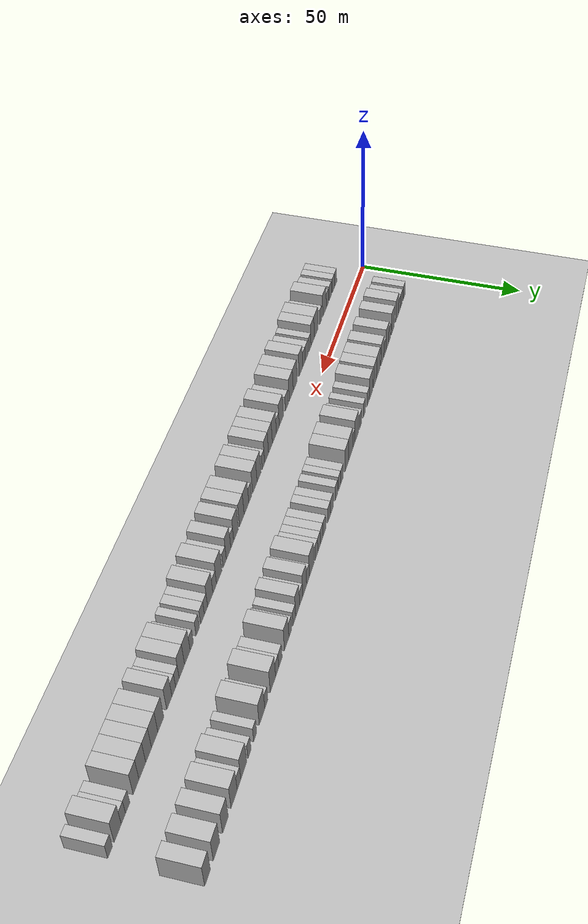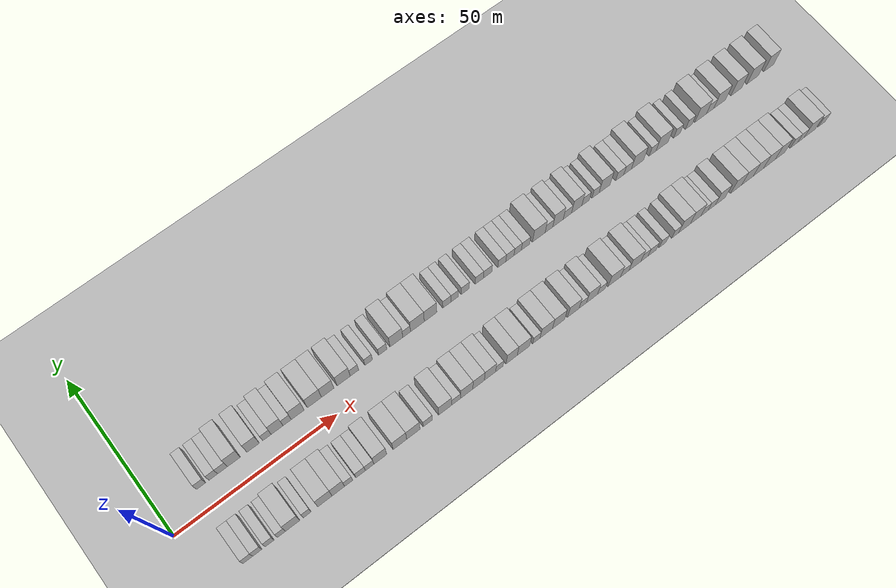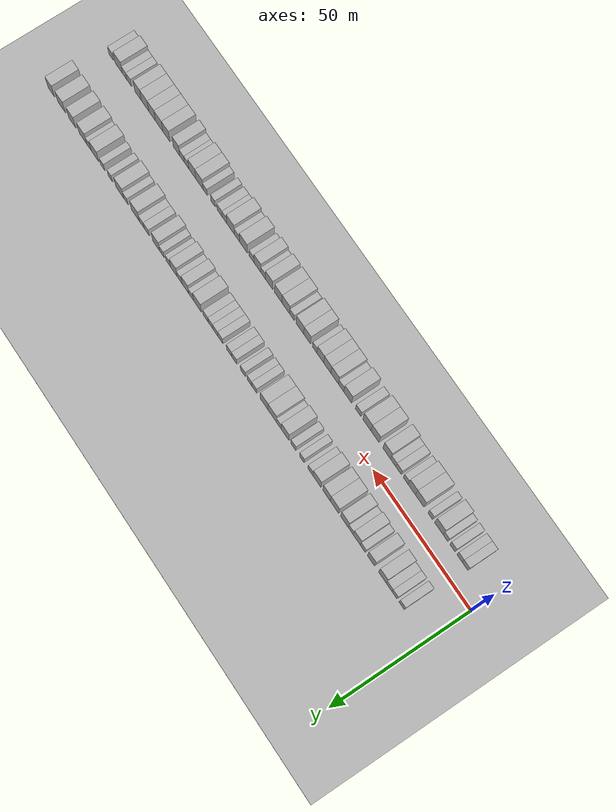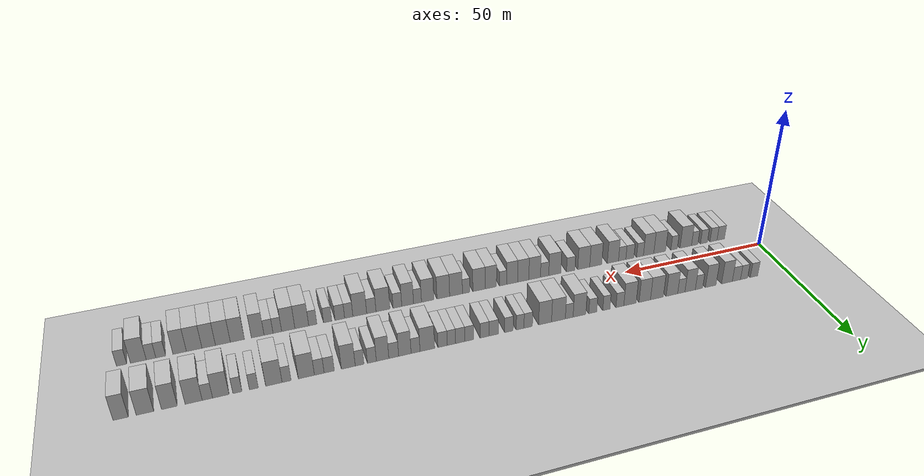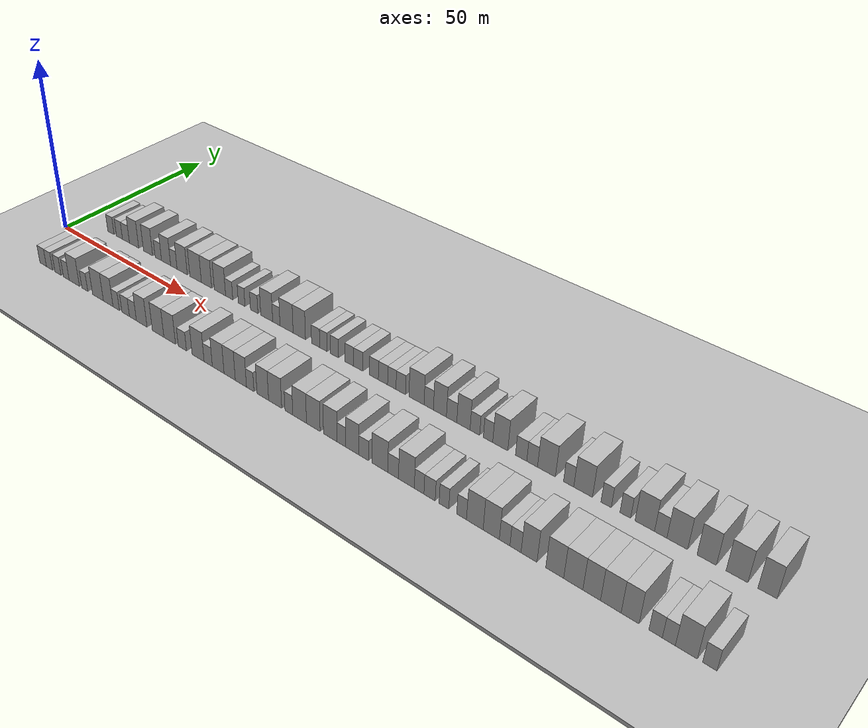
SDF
<?xml version="1.0" encoding="utf-8"?>

<sdf version="1.6">

   <world name="default">

      <gui fullscreen="0">

         <camera name="user_camera">

            <pose>-15 0 4.57585 0 0 0</pose>

            <view_controller>orbit</view_controller>

         </camera>

      </gui>

      <scene>

         <sky>

           <clouds>

             <speed>12</speed>

           </clouds>

         </sky>

         <ambient>0.4 0.4 0.4 1</ambient>

         <background>0.7 0.7 0.7 1</background>

         <shadows>1</shadows>

      </scene>

      <gravity>0 0 -9.8066</gravity>

      <magnetic_field>6e-06 2.3e-05 -4.2e-05</magnetic_field>

      <physics default="0" name="default_physics" type="ode">

         <ode>

            <solver>

               <type>quick</type>

               <iters>10</iters>

               <sor>1.0</sor>

               <use_dynamic_moi_rescaling>0</use_dynamic_moi_rescaling>

            </solver>

            <constraints>

               <cfm>0</cfm>

               <erp>0.2</erp>

               <contact_max_correcting_vel>100</contact_max_correcting_vel>

               <contact_surface_layer>0.001</contact_surface_layer>

            </constraints>

         </ode>

         <max_step_size>0.004</max_step_size>

         <real_time_factor>1</real_time_factor>

         <real_time_update_rate>250</real_time_update_rate>

      </physics>

      <light name="sun" type="directional">

         <cast_shadows>1</cast_shadows>

         <pose>0 0 10 0 0 0</pose>

         <diffuse>0.8 0.8 0.8 1</diffuse>

         <specular>0.2 0.2 0.2 1</specular>

         <attenuation>

            <range>1000</range>

            <constant>0.9</constant>

            <linear>0.01</linear>

            <quadratic>0.001</quadratic>

         </attenuation>

         <direction>-0.5 0.1 -0.9</direction>

      </light>

      <include>

         <name>ground_plane_1</name>

         <uri>model://HANNAS_ground_plane</uri>

         <pose>0 0 0  0 0 0</pose>

      </include>

      <include>

         <name>ground_plane_2</name>

         <uri>model://HANNAS_ground_plane</uri>

         <pose>100 0 0  0 0 0</pose>

      </include>

      <model name="building_1">

         <static>1</static>

         <pose frame="">12.3593 11.0000 0 0.000000 0.000000 1.570796</pose>

         <link name="link">

            <pose frame="">0 0 3.00 0 0 0</pose>

            <collision name="collision">

               <geometry>

                  <box>

                     <size>10.0000 2.7185 6.0000</size>

                  </box>

               </geometry>

               <max_contacts>10</max_contacts>

               <surface>

                  <contact>

                     <ode/>

                  </contact>

                  <bounce/>

                  <friction>

                     <torsional>

                        <ode/>

                     </torsional>

                     <ode/>

                  </friction>

               </surface>

            </collision>

            <visual name="visual">

               <cast_shadows>0</cast_shadows>

               <geometry>

                  <box>

                     <size>10.0000 2.7185 6.0000</size>

                  </box>

               </geometry>

               <material>

                  <script>

                     <uri>model://HANNAS_wall/materials/scripts</uri>

                     <uri>model://HANNAS_wall/materials/textures</uri>

                     <name>vrc/HANNAS_wall</name>

                  </script>

               </material>

            </visual>

            <self_collide>0</self_collide>

            <enable_wind>0</enable_wind>

            <kinematic>0</kinematic>

         </link>

      </model>

      <model name="building_2">

         <static>1</static>

         <pose frame="">16.0217 11.0000 0 0.000000 0.000000 1.570796</pose>

         <link name="link">

            <pose frame="">0 0 3.00 0 0 0</pose>

            <collision name="collision">

               <geometry>

                  <box>

                     <size>10.0000 2.6065 6.0000</size>

                  </box>

               </geometry>

               <max_contacts>10</max_contacts>

               <surface>

                  <contact>

                     <ode/>

                  </contact>

                  <bounce/>

                  <friction>

                     <torsional>

                        <ode/>

                     </torsional>

                     <ode/>

                  </friction>

               </surface>

            </collision>

            <visual name="visual">

               <cast_shadows>0</cast_shadows>

               <geometry>

                  <box>

                     <size>10.0000 2.6065 6.0000</size>

                  </box>

               </geometry>

               <material>

                  <script>

                     <uri>model://HANNAS_wall/materials/scripts</uri>

                     <uri>model://HANNAS_wall/materials/textures</uri>

                     <name>vrc/HANNAS_wall</name>

                  </script>

               </material>

            </visual>

            <self_collide>0</self_collide>

            <enable_wind>0</enable_wind>

            <kinematic>0</kinematic>

         </link>

      </model>

      <model name="building_3">

         <static>1</static>

         <pose frame="">18.8137 11.0000 0 0.000000 0.000000 1.570796</pose>

         <link name="link">

            <pose frame="">0 0 3.00 0 0 0</pose>

            <collision name="collision">

               <geometry>

                  <box>

                     <size>10.0000 2.9775 6.0000</size>

                  </box>

               </geometry>

               <max_contacts>10</max_contacts>

               <surface>

                  <contact>

                     <ode/>

                  </contact>

                  <bounce/>

                  <friction>

                     <torsional>

                        <ode/>

                     </torsional>

                     <ode/>

                  </friction>

               </surface>

            </collision>

            <visual name="visual">

               <cast_shadows>0</cast_shadows>

               <geometry>

                  <box>

                     <size>10.0000 2.9775 6.0000</size>

                  </box>

               </geometry>

               <material>

                  <script>

                     <uri>model://HANNAS_wall/materials/scripts</uri>

                     <uri>model://HANNAS_wall/materials/textures</uri>

                     <name>vrc/HANNAS_wall</name>

                  </script>

               </material>

            </visual>

            <self_collide>0</self_collide>

            <enable_wind>0</enable_wind>

            <kinematic>0</kinematic>

         </link>

      </model>

      <model name="building_4">

         <static>1</static>

         <pose frame="">22.2599 11.0000 0 0.000000 0.000000 1.570796</pose>

         <link name="link">

            <pose frame="">0 0 4.50 0 0 0</pose>

            <collision name="collision">

               <geometry>

                  <box>

                     <size>10.0000 3.9149 9.0000</size>

                  </box>

               </geometry>

               <max_contacts>10</max_contacts>

               <surface>

                  <contact>

                     <ode/>

                  </contact>

                  <bounce/>

                  <friction>

                     <torsional>

                        <ode/>

                     </torsional>

                     <ode/>

                  </friction>

               </surface>

            </collision>

            <visual name="visual">

               <cast_shadows>0</cast_shadows>

               <geometry>

                  <box>

                     <size>10.0000 3.9149 9.0000</size>

                  </box>

               </geometry>

               <material>

                  <script>

                     <uri>model://HANNAS_wall/materials/scripts</uri>

                     <uri>model://HANNAS_wall/materials/textures</uri>

                     <name>vrc/HANNAS_wall</name>

                  </script>

               </material>

            </visual>

            <self_collide>0</self_collide>

            <enable_wind>0</enable_wind>

            <kinematic>0</kinematic>

         </link>

      </model>

      <model name="building_5">

         <static>1</static>

         <pose frame="">28.1129 11.0000 0 0.000000 0.000000 1.570796</pose>

         <link name="link">

            <pose frame="">0 0 4.50 0 0 0</pose>

            <collision name="collision">

               <geometry>

                  <box>

                     <size>10.0000 3.7910 9.0000</size>

                  </box>

               </geometry>

               <max_contacts>10</max_contacts>

               <surface>

                  <contact>

                     <ode/>

                  </contact>

                  <bounce/>

                  <friction>

                     <torsional>

                        <ode/>

                     </torsional>

                     <ode/>

                  </friction>

               </surface>

            </collision>

            <visual name="visual">

               <cast_shadows>0</cast_shadows>

               <geometry>

                  <box>

                     <size>10.0000 3.7910 9.0000</size>

                  </box>

               </geometry>

               <material>

                  <script>

                     <uri>model://HANNAS_wall/materials/scripts</uri>

                     <uri>model://HANNAS_wall/materials/textures</uri>

                     <name>vrc/HANNAS_wall</name>

                  </script>

               </material>

            </visual>

            <self_collide>0</self_collide>

            <enable_wind>0</enable_wind>

            <kinematic>0</kinematic>

         </link>

      </model>

      <model name="building_6">

         <static>1</static>

         <pose frame="">32.3112 11.0000 0 0.000000 0.000000 1.570796</pose>

         <link name="link">

            <pose frame="">0 0 3.00 0 0 0</pose>

            <collision name="collision">

               <geometry>

                  <box>

                     <size>10.0000 2.6057 6.0000</size>

                  </box>

               </geometry>

               <max_contacts>10</max_contacts>

               <surface>

                  <contact>

                     <ode/>

                  </contact>

                  <bounce/>

                  <friction>

                     <torsional>

                        <ode/>

                     </torsional>

                     <ode/>

                  </friction>

               </surface>

            </collision>

            <visual name="visual">

               <cast_shadows>0</cast_shadows>

               <geometry>

                  <box>

                     <size>10.0000 2.6057 6.0000</size>

                  </box>

               </geometry>

               <material>

                  <script>

                     <uri>model://HANNAS_wall/materials/scripts</uri>

                     <uri>model://HANNAS_wall/materials/textures</uri>

                     <name>vrc/HANNAS_wall</name>

                  </script>

               </material>

            </visual>

            <self_collide>0</self_collide>

            <enable_wind>0</enable_wind>

            <kinematic>0</kinematic>

         </link>

      </model>

      <model name="building_7">

         <static>1</static>

         <pose frame="">35.4531 11.0000 0 0.000000 0.000000 1.570796</pose>

         <link name="link">

            <pose frame="">0 0 4.50 0 0 0</pose>

            <collision name="collision">

               <geometry>

                  <box>

                     <size>10.0000 3.6782 9.0000</size>

                  </box>

               </geometry>

               <max_contacts>10</max_contacts>

               <surface>

                  <contact>

                     <ode/>

                  </contact>

                  <bounce/>

                  <friction>

                     <torsional>

                        <ode/>

                     </torsional>

                     <ode/>

                  </friction>

               </surface>

            </collision>

            <visual name="visual">

               <cast_shadows>0</cast_shadows>

               <geometry>

                  <box>

                     <size>10.0000 3.6782 9.0000</size>

                  </box>

               </geometry>

               <material>

                  <script>

                     <uri>model://HANNAS_wall/materials/scripts</uri>

                     <uri>model://HANNAS_wall/materials/textures</uri>

                     <name>vrc/HANNAS_wall</name>

                  </script>

               </material>

            </visual>

            <self_collide>0</self_collide>

            <enable_wind>0</enable_wind>

            <kinematic>0</kinematic>

         </link>

      </model>

      <model name="building_8">

         <static>1</static>

         <pose frame="">38.5701 11.0000 0 0.000000 0.000000 1.570796</pose>

         <link name="link">

            <pose frame="">0 0 3.00 0 0 0</pose>

            <collision name="collision">

               <geometry>

                  <box>

                     <size>10.0000 2.5557 6.0000</size>

                  </box>

               </geometry>

               <max_contacts>10</max_contacts>

               <surface>

                  <contact>

                     <ode/>

                  </contact>

                  <bounce/>

                  <friction>

                     <torsional>

                        <ode/>

                     </torsional>

                     <ode/>

                  </friction>

               </surface>

            </collision>

            <visual name="visual">

               <cast_shadows>0</cast_shadows>

               <geometry>

                  <box>

                     <size>10.0000 2.5557 6.0000</size>

                  </box>

               </geometry>

               <material>

                  <script>

                     <uri>model://HANNAS_wall/materials/scripts</uri>

                     <uri>model://HANNAS_wall/materials/textures</uri>

                     <name>vrc/HANNAS_wall</name>

                  </script>

               </material>

            </visual>

            <self_collide>0</self_collide>

            <enable_wind>0</enable_wind>

            <kinematic>0</kinematic>

         </link>

      </model>

      <model name="building_9">

         <static>1</static>

         <pose frame="">41.8606 11.0000 0 0.000000 0.000000 1.570796</pose>

         <link name="link">

            <pose frame="">0 0 4.50 0 0 0</pose>

            <collision name="collision">

               <geometry>

                  <box>

                     <size>10.0000 4.0254 9.0000</size>

                  </box>

               </geometry>

               <max_contacts>10</max_contacts>

               <surface>

                  <contact>

                     <ode/>

                  </contact>

                  <bounce/>

                  <friction>

                     <torsional>

                        <ode/>

                     </torsional>

                     <ode/>

                  </friction>

               </surface>

            </collision>

            <visual name="visual">

               <cast_shadows>0</cast_shadows>

               <geometry>

                  <box>

                     <size>10.0000 4.0254 9.0000</size>

                  </box>

               </geometry>

               <material>

                  <script>

                     <uri>model://HANNAS_wall/materials/scripts</uri>

                     <uri>model://HANNAS_wall/materials/textures</uri>

                     <name>vrc/HANNAS_wall</name>

                  </script>

               </material>

            </visual>

            <self_collide>0</self_collide>

            <enable_wind>0</enable_wind>

            <kinematic>0</kinematic>

         </link>

      </model>

      <model name="building_10">

         <static>1</static>

         <pose frame="">47.0962 11.0000 0 0.000000 0.000000 1.570796</pose>

         <link name="link">

            <pose frame="">0 0 4.50 0 0 0</pose>

            <collision name="collision">

               <geometry>

                  <box>

                     <size>10.0000 4.4458 9.0000</size>

                  </box>

               </geometry>

               <max_contacts>10</max_contacts>

               <surface>

                  <contact>

                     <ode/>

                  </contact>

                  <bounce/>

                  <friction>

                     <torsional>

                        <ode/>

                     </torsional>

                     <ode/>

                  </friction>

               </surface>

            </collision>

            <visual name="visual">

               <cast_shadows>0</cast_shadows>

               <geometry>

                  <box>

                     <size>10.0000 4.4458 9.0000</size>

                  </box>

               </geometry>

               <material>

                  <script>

                     <uri>model://HANNAS_wall/materials/scripts</uri>

                     <uri>model://HANNAS_wall/materials/textures</uri>

                     <name>vrc/HANNAS_wall</name>

                  </script>

               </material>

            </visual>

            <self_collide>0</self_collide>

            <enable_wind>0</enable_wind>

            <kinematic>0</kinematic>

         </link>

      </model>

      <model name="building_11">

         <static>1</static>

         <pose frame="">51.2777 11.0000 0 0.000000 0.000000 1.570796</pose>

         <link name="link">

            <pose frame="">0 0 4.50 0 0 0</pose>

            <collision name="collision">

               <geometry>

                  <box>

                     <size>10.0000 3.9171 9.0000</size>

                  </box>

               </geometry>

               <max_contacts>10</max_contacts>

               <surface>

                  <contact>

                     <ode/>

                  </contact>

                  <bounce/>

                  <friction>

                     <torsional>

                        <ode/>

                     </torsional>

                     <ode/>

                  </friction>

               </surface>

            </collision>

            <visual name="visual">

               <cast_shadows>0</cast_shadows>

               <geometry>

                  <box>

                     <size>10.0000 3.9171 9.0000</size>

                  </box>

               </geometry>

               <material>

                  <script>

                     <uri>model://HANNAS_wall/materials/scripts</uri>

                     <uri>model://HANNAS_wall/materials/textures</uri>

                     <name>vrc/HANNAS_wall</name>

                  </script>

               </material>

            </visual>

            <self_collide>0</self_collide>

            <enable_wind>0</enable_wind>

            <kinematic>0</kinematic>

         </link>

      </model>

      <model name="building_12">

         <static>1</static>

         <pose frame="">56.3384 11.0000 0 0.000000 0.000000 1.570796</pose>

         <link name="link">

            <pose frame="">0 0 4.50 0 0 0</pose>

            <collision name="collision">

               <geometry>

                  <box>

                     <size>10.0000 4.2043 9.0000</size>

                  </box>

               </geometry>

               <max_contacts>10</max_contacts>

               <surface>

                  <contact>

                     <ode/>

                  </contact>

                  <bounce/>

                  <friction>

                     <torsional>

                        <ode/>

                     </torsional>

                     <ode/>

                  </friction>

               </surface>

            </collision>

            <visual name="visual">

               <cast_shadows>0</cast_shadows>

               <geometry>

                  <box>

                     <size>10.0000 4.2043 9.0000</size>

                  </box>

               </geometry>

               <material>

                  <script>

                     <uri>model://HANNAS_wall/materials/scripts</uri>

                     <uri>model://HANNAS_wall/materials/textures</uri>

                     <name>vrc/HANNAS_wall</name>

                  </script>

               </material>

            </visual>

            <self_collide>0</self_collide>

            <enable_wind>0</enable_wind>

            <kinematic>0</kinematic>

         </link>

      </model>

      <model name="building_13">

         <static>1</static>

         <pose frame="">59.7676 11.0000 0 0.000000 0.000000 1.570796</pose>

         <link name="link">

            <pose frame="">0 0 3.00 0 0 0</pose>

            <collision name="collision">

               <geometry>

                  <box>

                     <size>10.0000 2.6540 6.0000</size>

                  </box>

               </geometry>

               <max_contacts>10</max_contacts>

               <surface>

                  <contact>

                     <ode/>

                  </contact>

                  <bounce/>

                  <friction>

                     <torsional>

                        <ode/>

                     </torsional>

                     <ode/>

                  </friction>

               </surface>

            </collision>

            <visual name="visual">

               <cast_shadows>0</cast_shadows>

               <geometry>

                  <box>

                     <size>10.0000 2.6540 6.0000</size>

                  </box>

               </geometry>

               <material>

                  <script>

                     <uri>model://HANNAS_wall/materials/scripts</uri>

                     <uri>model://HANNAS_wall/materials/textures</uri>

                     <name>vrc/HANNAS_wall</name>

                  </script>

               </material>

            </visual>

            <self_collide>0</self_collide>

            <enable_wind>0</enable_wind>

            <kinematic>0</kinematic>

         </link>

      </model>

      <model name="building_14">

         <static>1</static>

         <pose frame="">64.3065 11.0000 0 0.000000 0.000000 1.570796</pose>

         <link name="link">

            <pose frame="">0 0 3.00 0 0 0</pose>

            <collision name="collision">

               <geometry>

                  <box>

                     <size>10.0000 2.4238 6.0000</size>

                  </box>

               </geometry>

               <max_contacts>10</max_contacts>

               <surface>

                  <contact>

                     <ode/>

                  </contact>

                  <bounce/>

                  <friction>

                     <torsional>

                        <ode/>

                     </torsional>

                     <ode/>

                  </friction>

               </surface>

            </collision>

            <visual name="visual">

               <cast_shadows>0</cast_shadows>

               <geometry>

                  <box>

                     <size>10.0000 2.4238 6.0000</size>

                  </box>

               </geometry>

               <material>

                  <script>

                     <uri>model://HANNAS_wall/materials/scripts</uri>

                     <uri>model://HANNAS_wall/materials/textures</uri>

                     <name>vrc/HANNAS_wall</name>

                  </script>

               </material>

            </visual>

            <self_collide>0</self_collide>

            <enable_wind>0</enable_wind>

            <kinematic>0</kinematic>

         </link>

      </model>

      <model name="building_15">

         <static>1</static>

         <pose frame="">68.8407 11.0000 0 0.000000 0.000000 1.570796</pose>

         <link name="link">

            <pose frame="">0 0 3.00 0 0 0</pose>

            <collision name="collision">

               <geometry>

                  <box>

                     <size>10.0000 2.6445 6.0000</size>

                  </box>

               </geometry>

               <max_contacts>10</max_contacts>

               <surface>

                  <contact>

                     <ode/>

                  </contact>

                  <bounce/>

                  <friction>

                     <torsional>

                        <ode/>

                     </torsional>

                     <ode/>

                  </friction>

               </surface>

            </collision>

            <visual name="visual">

               <cast_shadows>0</cast_shadows>

               <geometry>

                  <box>

                     <size>10.0000 2.6445 6.0000</size>

                  </box>

               </geometry>

               <material>

                  <script>

                     <uri>model://HANNAS_wall/materials/scripts</uri>

                     <uri>model://HANNAS_wall/materials/textures</uri>

                     <name>vrc/HANNAS_wall</name>

                  </script>

               </material>

            </visual>

            <self_collide>0</self_collide>

            <enable_wind>0</enable_wind>

            <kinematic>0</kinematic>

         </link>

      </model>

      <model name="building_16">

         <static>1</static>

         <pose frame="">73.2525 11.0000 0 0.000000 0.000000 1.570796</pose>

         <link name="link">

            <pose frame="">0 0 4.50 0 0 0</pose>

            <collision name="collision">

               <geometry>

                  <box>

                     <size>10.0000 4.1791 9.0000</size>

                  </box>

               </geometry>

               <max_contacts>10</max_contacts>

               <surface>

                  <contact>

                     <ode/>

                  </contact>

                  <bounce/>

                  <friction>

                     <torsional>

                        <ode/>

                     </torsional>

                     <ode/>

                  </friction>

               </surface>

            </collision>

            <visual name="visual">

               <cast_shadows>0</cast_shadows>

               <geometry>

                  <box>

                     <size>10.0000 4.1791 9.0000</size>

                  </box>

               </geometry>

               <material>

                  <script>

                     <uri>model://HANNAS_wall/materials/scripts</uri>

                     <uri>model://HANNAS_wall/materials/textures</uri>

                     <name>vrc/HANNAS_wall</name>

                  </script>

               </material>

            </visual>

            <self_collide>0</self_collide>

            <enable_wind>0</enable_wind>

            <kinematic>0</kinematic>

         </link>

      </model>

      <model name="building_17">

         <static>1</static>

         <pose frame="">76.6063 11.0000 0 0.000000 0.000000 1.570796</pose>

         <link name="link">

            <pose frame="">0 0 3.00 0 0 0</pose>

            <collision name="collision">

               <geometry>

                  <box>

                     <size>10.0000 2.5286 6.0000</size>

                  </box>

               </geometry>

               <max_contacts>10</max_contacts>

               <surface>

                  <contact>

                     <ode/>

                  </contact>

                  <bounce/>

                  <friction>

                     <torsional>

                        <ode/>

                     </torsional>

                     <ode/>

                  </friction>

               </surface>

            </collision>

            <visual name="visual">

               <cast_shadows>0</cast_shadows>

               <geometry>

                  <box>

                     <size>10.0000 2.5286 6.0000</size>

                  </box>

               </geometry>

               <material>

                  <script>

                     <uri>model://HANNAS_wall/materials/scripts</uri>

                     <uri>model://HANNAS_wall/materials/textures</uri>

                     <name>vrc/HANNAS_wall</name>

                  </script>

               </material>

            </visual>

            <self_collide>0</self_collide>

            <enable_wind>0</enable_wind>

            <kinematic>0</kinematic>

         </link>

      </model>

      <model name="building_18">

         <static>1</static>

         <pose frame="">80.1111 11.0000 0 0.000000 0.000000 1.570796</pose>

         <link name="link">

            <pose frame="">0 0 4.50 0 0 0</pose>

            <collision name="collision">

               <geometry>

                  <box>

                     <size>10.0000 4.4809 9.0000</size>

                  </box>

               </geometry>

               <max_contacts>10</max_contacts>

               <surface>

                  <contact>

                     <ode/>

                  </contact>

                  <bounce/>

                  <friction>

                     <torsional>

                        <ode/>

                     </torsional>

                     <ode/>

                  </friction>

               </surface>

            </collision>

            <visual name="visual">

               <cast_shadows>0</cast_shadows>

               <geometry>

                  <box>

                     <size>10.0000 4.4809 9.0000</size>

                  </box>

               </geometry>

               <material>

                  <script>

                     <uri>model://HANNAS_wall/materials/scripts</uri>

                     <uri>model://HANNAS_wall/materials/textures</uri>

                     <name>vrc/HANNAS_wall</name>

                  </script>

               </material>

            </visual>

            <self_collide>0</self_collide>

            <enable_wind>0</enable_wind>

            <kinematic>0</kinematic>

         </link>

      </model>

      <model name="building_19">

         <static>1</static>

         <pose frame="">84.4276 11.0000 0 0.000000 0.000000 1.570796</pose>

         <link name="link">

            <pose frame="">0 0 4.50 0 0 0</pose>

            <collision name="collision">

               <geometry>

                  <box>

                     <size>10.0000 4.1520 9.0000</size>

                  </box>

               </geometry>

               <max_contacts>10</max_contacts>

               <surface>

                  <contact>

                     <ode/>

                  </contact>

                  <bounce/>

                  <friction>

                     <torsional>

                        <ode/>

                     </torsional>

                     <ode/>

                  </friction>

               </surface>

            </collision>

            <visual name="visual">

               <cast_shadows>0</cast_shadows>

               <geometry>

                  <box>

                     <size>10.0000 4.1520 9.0000</size>

                  </box>

               </geometry>

               <material>

                  <script>

                     <uri>model://HANNAS_wall/materials/scripts</uri>

                     <uri>model://HANNAS_wall/materials/textures</uri>

                     <name>vrc/HANNAS_wall</name>

                  </script>

               </material>

            </visual>

            <self_collide>0</self_collide>

            <enable_wind>0</enable_wind>

            <kinematic>0</kinematic>

         </link>

      </model>

      <model name="building_20">

         <static>1</static>

         <pose frame="">89.8496 11.0000 0 0.000000 0.000000 1.570796</pose>

         <link name="link">

            <pose frame="">0 0 3.00 0 0 0</pose>

            <collision name="collision">

               <geometry>

                  <box>

                     <size>10.0000 2.6919 6.0000</size>

                  </box>

               </geometry>

               <max_contacts>10</max_contacts>

               <surface>

                  <contact>

                     <ode/>

                  </contact>

                  <bounce/>

                  <friction>

                     <torsional>

                        <ode/>

                     </torsional>

                     <ode/>

                  </friction>

               </surface>

            </collision>

            <visual name="visual">

               <cast_shadows>0</cast_shadows>

               <geometry>

                  <box>

                     <size>10.0000 2.6919 6.0000</size>

                  </box>

               </geometry>

               <material>

                  <script>

                     <uri>model://HANNAS_wall/materials/scripts</uri>

                     <uri>model://HANNAS_wall/materials/textures</uri>

                     <name>vrc/HANNAS_wall</name>

                  </script>

               </material>

            </visual>

            <self_collide>0</self_collide>

            <enable_wind>0</enable_wind>

            <kinematic>0</kinematic>

         </link>

      </model>

      <model name="building_21">

         <static>1</static>

         <pose frame="">92.4161 11.0000 0 0.000000 0.000000 1.570796</pose>

         <link name="link">

            <pose frame="">0 0 3.00 0 0 0</pose>

            <collision name="collision">

               <geometry>

                  <box>

                     <size>10.0000 2.4411 6.0000</size>

                  </box>

               </geometry>

               <max_contacts>10</max_contacts>

               <surface>

                  <contact>

                     <ode/>

                  </contact>

                  <bounce/>

                  <friction>

                     <torsional>

                        <ode/>

                     </torsional>

                     <ode/>

                  </friction>

               </surface>

            </collision>

            <visual name="visual">

               <cast_shadows>0</cast_shadows>

               <geometry>

                  <box>

                     <size>10.0000 2.4411 6.0000</size>

                  </box>

               </geometry>

               <material>

                  <script>

                     <uri>model://HANNAS_wall/materials/scripts</uri>

                     <uri>model://HANNAS_wall/materials/textures</uri>

                     <name>vrc/HANNAS_wall</name>

                  </script>

               </material>

            </visual>

            <self_collide>0</self_collide>

            <enable_wind>0</enable_wind>

            <kinematic>0</kinematic>

         </link>

      </model>

      <model name="building_22">

         <static>1</static>

         <pose frame="">95.9638 11.0000 0 0.000000 0.000000 1.570796</pose>

         <link name="link">

            <pose frame="">0 0 3.00 0 0 0</pose>

            <collision name="collision">

               <geometry>

                  <box>

                     <size>10.0000 2.6543 6.0000</size>

                  </box>

               </geometry>

               <max_contacts>10</max_contacts>

               <surface>

                  <contact>

                     <ode/>

                  </contact>

                  <bounce/>

                  <friction>

                     <torsional>

                        <ode/>

                     </torsional>

                     <ode/>

                  </friction>

               </surface>

            </collision>

            <visual name="visual">

               <cast_shadows>0</cast_shadows>

               <geometry>

                  <box>

                     <size>10.0000 2.6543 6.0000</size>

                  </box>

               </geometry>

               <material>

                  <script>

                     <uri>model://HANNAS_wall/materials/scripts</uri>

                     <uri>model://HANNAS_wall/materials/textures</uri>

                     <name>vrc/HANNAS_wall</name>

                  </script>

               </material>

            </visual>

            <self_collide>0</self_collide>

            <enable_wind>0</enable_wind>

            <kinematic>0</kinematic>

         </link>

      </model>

      <model name="building_23">

         <static>1</static>

         <pose frame="">100.6855 11.0000 0 0.000000 0.000000 1.570796</pose>

         <link name="link">

            <pose frame="">0 0 3.00 0 0 0</pose>

            <collision name="collision">

               <geometry>

                  <box>

                     <size>10.0000 2.7892 6.0000</size>

                  </box>

               </geometry>

               <max_contacts>10</max_contacts>

               <surface>

                  <contact>

                     <ode/>

                  </contact>

                  <bounce/>

                  <friction>

                     <torsional>

                        <ode/>

                     </torsional>

                     <ode/>

                  </friction>

               </surface>

            </collision>

            <visual name="visual">

               <cast_shadows>0</cast_shadows>

               <geometry>

                  <box>

                     <size>10.0000 2.7892 6.0000</size>

                  </box>

               </geometry>

               <material>

                  <script>

                     <uri>model://HANNAS_wall/materials/scripts</uri>

                     <uri>model://HANNAS_wall/materials/textures</uri>

                     <name>vrc/HANNAS_wall</name>

                  </script>

               </material>

            </visual>

            <self_collide>0</self_collide>

            <enable_wind>0</enable_wind>

            <kinematic>0</kinematic>

         </link>

      </model>

      <model name="building_24">

         <static>1</static>

         <pose frame="">103.5084 11.0000 0 0.000000 0.000000 1.570796</pose>

         <link name="link">

            <pose frame="">0 0 3.00 0 0 0</pose>

            <collision name="collision">

               <geometry>

                  <box>

                     <size>10.0000 2.8566 6.0000</size>

                  </box>

               </geometry>

               <max_contacts>10</max_contacts>

               <surface>

                  <contact>

                     <ode/>

                  </contact>

                  <bounce/>

                  <friction>

                     <torsional>

                        <ode/>

                     </torsional>

                     <ode/>

                  </friction>

               </surface>

            </collision>

            <visual name="visual">

               <cast_shadows>0</cast_shadows>

               <geometry>

                  <box>

                     <size>10.0000 2.8566 6.0000</size>

                  </box>

               </geometry>

               <material>

                  <script>

                     <uri>model://HANNAS_wall/materials/scripts</uri>

                     <uri>model://HANNAS_wall/materials/textures</uri>

                     <name>vrc/HANNAS_wall</name>

                  </script>

               </material>

            </visual>

            <self_collide>0</self_collide>

            <enable_wind>0</enable_wind>

            <kinematic>0</kinematic>

         </link>

      </model>

      <model name="building_25">

         <static>1</static>

         <pose frame="">108.2982 11.0000 0 0.000000 0.000000 1.570796</pose>

         <link name="link">

            <pose frame="">0 0 3.00 0 0 0</pose>

            <collision name="collision">

               <geometry>

                  <box>

                     <size>10.0000 2.7230 6.0000</size>

                  </box>

               </geometry>

               <max_contacts>10</max_contacts>

               <surface>

                  <contact>

                     <ode/>

                  </contact>

                  <bounce/>

                  <friction>

                     <torsional>

                        <ode/>

                     </torsional>

                     <ode/>

                  </friction>

               </surface>

            </collision>

            <visual name="visual">

               <cast_shadows>0</cast_shadows>

               <geometry>

                  <box>

                     <size>10.0000 2.7230 6.0000</size>

                  </box>

               </geometry>

               <material>

                  <script>

                     <uri>model://HANNAS_wall/materials/scripts</uri>

                     <uri>model://HANNAS_wall/materials/textures</uri>

                     <name>vrc/HANNAS_wall</name>

                  </script>

               </material>

            </visual>

            <self_collide>0</self_collide>

            <enable_wind>0</enable_wind>

            <kinematic>0</kinematic>

         </link>

      </model>

      <model name="building_26">

         <static>1</static>

         <pose frame="">111.0594 11.0000 0 0.000000 0.000000 1.570796</pose>

         <link name="link">

            <pose frame="">0 0 3.00 0 0 0</pose>

            <collision name="collision">

               <geometry>

                  <box>

                     <size>10.0000 2.7994 6.0000</size>

                  </box>

               </geometry>

               <max_contacts>10</max_contacts>

               <surface>

                  <contact>

                     <ode/>

                  </contact>

                  <bounce/>

                  <friction>

                     <torsional>

                        <ode/>

                     </torsional>

                     <ode/>

                  </friction>

               </surface>

            </collision>

            <visual name="visual">

               <cast_shadows>0</cast_shadows>

               <geometry>

                  <box>

                     <size>10.0000 2.7994 6.0000</size>

                  </box>

               </geometry>

               <material>

                  <script>

                     <uri>model://HANNAS_wall/materials/scripts</uri>

                     <uri>model://HANNAS_wall/materials/textures</uri>

                     <name>vrc/HANNAS_wall</name>

                  </script>

               </material>

            </visual>

            <self_collide>0</self_collide>

            <enable_wind>0</enable_wind>

            <kinematic>0</kinematic>

         </link>

      </model>

      <model name="building_27">

         <static>1</static>

         <pose frame="">113.7172 11.0000 0 0.000000 0.000000 1.570796</pose>

         <link name="link">

            <pose frame="">0 0 3.00 0 0 0</pose>

            <collision name="collision">

               <geometry>

                  <box>

                     <size>10.0000 2.5162 6.0000</size>

                  </box>

               </geometry>

               <max_contacts>10</max_contacts>

               <surface>

                  <contact>

                     <ode/>

                  </contact>

                  <bounce/>

                  <friction>

                     <torsional>

                        <ode/>

                     </torsional>

                     <ode/>

                  </friction>

               </surface>

            </collision>

            <visual name="visual">

               <cast_shadows>0</cast_shadows>

               <geometry>

                  <box>

                     <size>10.0000 2.5162 6.0000</size>

                  </box>

               </geometry>

               <material>

                  <script>

                     <uri>model://HANNAS_wall/materials/scripts</uri>

                     <uri>model://HANNAS_wall/materials/textures</uri>

                     <name>vrc/HANNAS_wall</name>

                  </script>

               </material>

            </visual>

            <self_collide>0</self_collide>

            <enable_wind>0</enable_wind>

            <kinematic>0</kinematic>

         </link>

      </model>

      <model name="building_28">

         <static>1</static>

         <pose frame="">116.3857 11.0000 0 0.000000 0.000000 1.570796</pose>

         <link name="link">

            <pose frame="">0 0 3.00 0 0 0</pose>

            <collision name="collision">

               <geometry>

                  <box>

                     <size>10.0000 2.8208 6.0000</size>

                  </box>

               </geometry>

               <max_contacts>10</max_contacts>

               <surface>

                  <contact>

                     <ode/>

                  </contact>

                  <bounce/>

                  <friction>

                     <torsional>

                        <ode/>

                     </torsional>

                     <ode/>

                  </friction>

               </surface>

            </collision>

            <visual name="visual">

               <cast_shadows>0</cast_shadows>

               <geometry>

                  <box>

                     <size>10.0000 2.8208 6.0000</size>

                  </box>

               </geometry>

               <material>

                  <script>

                     <uri>model://HANNAS_wall/materials/scripts</uri>

                     <uri>model://HANNAS_wall/materials/textures</uri>

                     <name>vrc/HANNAS_wall</name>

                  </script>

               </material>

            </visual>

            <self_collide>0</self_collide>

            <enable_wind>0</enable_wind>

            <kinematic>0</kinematic>

         </link>

      </model>

      <model name="building_29">

         <static>1</static>

         <pose frame="">120.9853 11.0000 0 0.000000 0.000000 1.570796</pose>

         <link name="link">

            <pose frame="">0 0 4.50 0 0 0</pose>

            <collision name="collision">

               <geometry>

                  <box>

                     <size>10.0000 4.3785 9.0000</size>

                  </box>

               </geometry>

               <max_contacts>10</max_contacts>

               <surface>

                  <contact>

                     <ode/>

                  </contact>

                  <bounce/>

                  <friction>

                     <torsional>

                        <ode/>

                     </torsional>

                     <ode/>

                  </friction>

               </surface>

            </collision>

            <visual name="visual">

               <cast_shadows>0</cast_shadows>

               <geometry>

                  <box>

                     <size>10.0000 4.3785 9.0000</size>

                  </box>

               </geometry>

               <material>

                  <script>

                     <uri>model://HANNAS_wall/materials/scripts</uri>

                     <uri>model://HANNAS_wall/materials/textures</uri>

                     <name>vrc/HANNAS_wall</name>

                  </script>

               </material>

            </visual>

            <self_collide>0</self_collide>

            <enable_wind>0</enable_wind>

            <kinematic>0</kinematic>

         </link>

      </model>

      <model name="building_30">

         <static>1</static>

         <pose frame="">124.4999 11.0000 0 0.000000 0.000000 1.570796</pose>

         <link name="link">

            <pose frame="">0 0 3.00 0 0 0</pose>

            <collision name="collision">

               <geometry>

                  <box>

                     <size>10.0000 2.6507 6.0000</size>

                  </box>

               </geometry>

               <max_contacts>10</max_contacts>

               <surface>

                  <contact>

                     <ode/>

                  </contact>

                  <bounce/>

                  <friction>

                     <torsional>

                        <ode/>

                     </torsional>

                     <ode/>

                  </friction>

               </surface>

            </collision>

            <visual name="visual">

               <cast_shadows>0</cast_shadows>

               <geometry>

                  <box>

                     <size>10.0000 2.6507 6.0000</size>

                  </box>

               </geometry>

               <material>

                  <script>

                     <uri>model://HANNAS_wall/materials/scripts</uri>

                     <uri>model://HANNAS_wall/materials/textures</uri>

                     <name>vrc/HANNAS_wall</name>

                  </script>

               </material>

            </visual>

            <self_collide>0</self_collide>

            <enable_wind>0</enable_wind>

            <kinematic>0</kinematic>

         </link>

      </model>

      <model name="building_31">

         <static>1</static>

         <pose frame="">127.6629 11.0000 0 0.000000 0.000000 1.570796</pose>

         <link name="link">

            <pose frame="">0 0 4.50 0 0 0</pose>

            <collision name="collision">

               <geometry>

                  <box>

                     <size>10.0000 3.6754 9.0000</size>

                  </box>

               </geometry>

               <max_contacts>10</max_contacts>

               <surface>

                  <contact>

                     <ode/>

                  </contact>

                  <bounce/>

                  <friction>

                     <torsional>

                        <ode/>

                     </torsional>

                     <ode/>

                  </friction>

               </surface>

            </collision>

            <visual name="visual">

               <cast_shadows>0</cast_shadows>

               <geometry>

                  <box>

                     <size>10.0000 3.6754 9.0000</size>

                  </box>

               </geometry>

               <material>

                  <script>

                     <uri>model://HANNAS_wall/materials/scripts</uri>

                     <uri>model://HANNAS_wall/materials/textures</uri>

                     <name>vrc/HANNAS_wall</name>

                  </script>

               </material>

            </visual>

            <self_collide>0</self_collide>

            <enable_wind>0</enable_wind>

            <kinematic>0</kinematic>

         </link>

      </model>

      <model name="building_32">

         <static>1</static>

         <pose frame="">130.9396 11.0000 0 0.000000 0.000000 1.570796</pose>

         <link name="link">

            <pose frame="">0 0 3.00 0 0 0</pose>

            <collision name="collision">

               <geometry>

                  <box>

                     <size>10.0000 2.8780 6.0000</size>

                  </box>

               </geometry>

               <max_contacts>10</max_contacts>

               <surface>

                  <contact>

                     <ode/>

                  </contact>

                  <bounce/>

                  <friction>

                     <torsional>

                        <ode/>

                     </torsional>

                     <ode/>

                  </friction>

               </surface>

            </collision>

            <visual name="visual">

               <cast_shadows>0</cast_shadows>

               <geometry>

                  <box>

                     <size>10.0000 2.8780 6.0000</size>

                  </box>

               </geometry>

               <material>

                  <script>

                     <uri>model://HANNAS_wall/materials/scripts</uri>

                     <uri>model://HANNAS_wall/materials/textures</uri>

                     <name>vrc/HANNAS_wall</name>

                  </script>

               </material>

            </visual>

            <self_collide>0</self_collide>

            <enable_wind>0</enable_wind>

            <kinematic>0</kinematic>

         </link>

      </model>

      <model name="building_33">

         <static>1</static>

         <pose frame="">134.2009 11.0000 0 0.000000 0.000000 1.570796</pose>

         <link name="link">

            <pose frame="">0 0 4.50 0 0 0</pose>

            <collision name="collision">

               <geometry>

                  <box>

                     <size>10.0000 3.6445 9.0000</size>

                  </box>

               </geometry>

               <max_contacts>10</max_contacts>

               <surface>

                  <contact>

                     <ode/>

                  </contact>

                  <bounce/>

                  <friction>

                     <torsional>

                        <ode/>

                     </torsional>

                     <ode/>

                  </friction>

               </surface>

            </collision>

            <visual name="visual">

               <cast_shadows>0</cast_shadows>

               <geometry>

                  <box>

                     <size>10.0000 3.6445 9.0000</size>

                  </box>

               </geometry>

               <material>

                  <script>

                     <uri>model://HANNAS_wall/materials/scripts</uri>

                     <uri>model://HANNAS_wall/materials/textures</uri>

                     <name>vrc/HANNAS_wall</name>

                  </script>

               </material>

            </visual>

            <self_collide>0</self_collide>

            <enable_wind>0</enable_wind>

            <kinematic>0</kinematic>

         </link>

      </model>

      <model name="building_34">

         <static>1</static>

         <pose frame="">137.3183 11.0000 0 0.000000 0.000000 1.570796</pose>

         <link name="link">

            <pose frame="">0 0 3.00 0 0 0</pose>

            <collision name="collision">

               <geometry>

                  <box>

                     <size>10.0000 2.5903 6.0000</size>

                  </box>

               </geometry>

               <max_contacts>10</max_contacts>

               <surface>

                  <contact>

                     <ode/>

                  </contact>

                  <bounce/>

                  <friction>

                     <torsional>

                        <ode/>

                     </torsional>

                     <ode/>

                  </friction>

               </surface>

            </collision>

            <visual name="visual">

               <cast_shadows>0</cast_shadows>

               <geometry>

                  <box>

                     <size>10.0000 2.5903 6.0000</size>

                  </box>

               </geometry>

               <material>

                  <script>

                     <uri>model://HANNAS_wall/materials/scripts</uri>

                     <uri>model://HANNAS_wall/materials/textures</uri>

                     <name>vrc/HANNAS_wall</name>

                  </script>

               </material>

            </visual>

            <self_collide>0</self_collide>

            <enable_wind>0</enable_wind>

            <kinematic>0</kinematic>

         </link>

      </model>

      <model name="building_35">

         <static>1</static>

         <pose frame="">140.8595 11.0000 0 0.000000 0.000000 1.570796</pose>

         <link name="link">

            <pose frame="">0 0 3.00 0 0 0</pose>

            <collision name="collision">

               <geometry>

                  <box>

                     <size>10.0000 2.4921 6.0000</size>

                  </box>

               </geometry>

               <max_contacts>10</max_contacts>

               <surface>

                  <contact>

                     <ode/>

                  </contact>

                  <bounce/>

                  <friction>

                     <torsional>

                        <ode/>

                     </torsional>

                     <ode/>

                  </friction>

               </surface>

            </collision>

            <visual name="visual">

               <cast_shadows>0</cast_shadows>

               <geometry>

                  <box>

                     <size>10.0000 2.4921 6.0000</size>

                  </box>

               </geometry>

               <material>

                  <script>

                     <uri>model://HANNAS_wall/materials/scripts</uri>

                     <uri>model://HANNAS_wall/materials/textures</uri>

                     <name>vrc/HANNAS_wall</name>

                  </script>

               </material>

            </visual>

            <self_collide>0</self_collide>

            <enable_wind>0</enable_wind>

            <kinematic>0</kinematic>

         </link>

      </model>

      <model name="building_36">

         <static>1</static>

         <pose frame="">144.0839 11.0000 0 0.000000 0.000000 1.570796</pose>

         <link name="link">

            <pose frame="">0 0 4.50 0 0 0</pose>

            <collision name="collision">

               <geometry>

                  <box>

                     <size>10.0000 3.9569 9.0000</size>

                  </box>

               </geometry>

               <max_contacts>10</max_contacts>

               <surface>

                  <contact>

                     <ode/>

                  </contact>

                  <bounce/>

                  <friction>

                     <torsional>

                        <ode/>

                     </torsional>

                     <ode/>

                  </friction>

               </surface>

            </collision>

            <visual name="visual">

               <cast_shadows>0</cast_shadows>

               <geometry>

                  <box>

                     <size>10.0000 3.9569 9.0000</size>

                  </box>

               </geometry>

               <material>

                  <script>

                     <uri>model://HANNAS_wall/materials/scripts</uri>

                     <uri>model://HANNAS_wall/materials/textures</uri>

                     <name>vrc/HANNAS_wall</name>

                  </script>

               </material>

            </visual>

            <self_collide>0</self_collide>

            <enable_wind>0</enable_wind>

            <kinematic>0</kinematic>

         </link>

      </model>

      <model name="building_37">

         <static>1</static>

         <pose frame="">149.5078 11.0000 0 0.000000 0.000000 1.570796</pose>

         <link name="link">

            <pose frame="">0 0 3.00 0 0 0</pose>

            <collision name="collision">

               <geometry>

                  <box>

                     <size>10.0000 2.8908 6.0000</size>

                  </box>

               </geometry>

               <max_contacts>10</max_contacts>

               <surface>

                  <contact>

                     <ode/>

                  </contact>

                  <bounce/>

                  <friction>

                     <torsional>

                        <ode/>

                     </torsional>

                     <ode/>

                  </friction>

               </surface>

            </collision>

            <visual name="visual">

               <cast_shadows>0</cast_shadows>

               <geometry>

                  <box>

                     <size>10.0000 2.8908 6.0000</size>

                  </box>

               </geometry>

               <material>

                  <script>

                     <uri>model://HANNAS_wall/materials/scripts</uri>

                     <uri>model://HANNAS_wall/materials/textures</uri>

                     <name>vrc/HANNAS_wall</name>

                  </script>

               </material>

            </visual>

            <self_collide>0</self_collide>

            <enable_wind>0</enable_wind>

            <kinematic>0</kinematic>

         </link>

      </model>

      <model name="building_38">

         <static>1</static>

         <pose frame="">152.3108 11.0000 0 0.000000 0.000000 1.570796</pose>

         <link name="link">

            <pose frame="">0 0 3.00 0 0 0</pose>

            <collision name="collision">

               <geometry>

                  <box>

                     <size>10.0000 2.7152 6.0000</size>

                  </box>

               </geometry>

               <max_contacts>10</max_contacts>

               <surface>

                  <contact>

                     <ode/>

                  </contact>

                  <bounce/>

                  <friction>

                     <torsional>

                        <ode/>

                     </torsional>

                     <ode/>

                  </friction>

               </surface>

            </collision>

            <visual name="visual">

               <cast_shadows>0</cast_shadows>

               <geometry>

                  <box>

                     <size>10.0000 2.7152 6.0000</size>

                  </box>

               </geometry>

               <material>

                  <script>

                     <uri>model://HANNAS_wall/materials/scripts</uri>

                     <uri>model://HANNAS_wall/materials/textures</uri>

                     <name>vrc/HANNAS_wall</name>

                  </script>

               </material>

            </visual>

            <self_collide>0</self_collide>

            <enable_wind>0</enable_wind>

            <kinematic>0</kinematic>

         </link>

      </model>

      <model name="building_39">

         <static>1</static>

         <pose frame="">155.8981 11.0000 0 0.000000 0.000000 1.570796</pose>

         <link name="link">

            <pose frame="">0 0 4.50 0 0 0</pose>

            <collision name="collision">

               <geometry>

                  <box>

                     <size>10.0000 4.4595 9.0000</size>

                  </box>

               </geometry>

               <max_contacts>10</max_contacts>

               <surface>

                  <contact>

                     <ode/>

                  </contact>

                  <bounce/>

                  <friction>

                     <torsional>

                        <ode/>

                     </torsional>

                     <ode/>

                  </friction>

               </surface>

            </collision>

            <visual name="visual">

               <cast_shadows>0</cast_shadows>

               <geometry>

                  <box>

                     <size>10.0000 4.4595 9.0000</size>

                  </box>

               </geometry>

               <material>

                  <script>

                     <uri>model://HANNAS_wall/materials/scripts</uri>

                     <uri>model://HANNAS_wall/materials/textures</uri>

                     <name>vrc/HANNAS_wall</name>

                  </script>

               </material>

            </visual>

            <self_collide>0</self_collide>

            <enable_wind>0</enable_wind>

            <kinematic>0</kinematic>

         </link>

      </model>

      <model name="building_40">

         <static>1</static>

         <pose frame="">161.3708 11.0000 0 0.000000 0.000000 1.570796</pose>

         <link name="link">

            <pose frame="">0 0 3.00 0 0 0</pose>

            <collision name="collision">

               <geometry>

                  <box>

                     <size>10.0000 2.4860 6.0000</size>

                  </box>

               </geometry>

               <max_contacts>10</max_contacts>

               <surface>

                  <contact>

                     <ode/>

                  </contact>

                  <bounce/>

                  <friction>

                     <torsional>

                        <ode/>

                     </torsional>

                     <ode/>

                  </friction>

               </surface>

            </collision>

            <visual name="visual">

               <cast_shadows>0</cast_shadows>

               <geometry>

                  <box>

                     <size>10.0000 2.4860 6.0000</size>

                  </box>

               </geometry>

               <material>

                  <script>

                     <uri>model://HANNAS_wall/materials/scripts</uri>

                     <uri>model://HANNAS_wall/materials/textures</uri>

                     <name>vrc/HANNAS_wall</name>

                  </script>

               </material>

            </visual>

            <self_collide>0</self_collide>

            <enable_wind>0</enable_wind>

            <kinematic>0</kinematic>

         </link>

      </model>

      <model name="building_41">

         <static>1</static>

         <pose frame="">164.8539 11.0000 0 0.000000 0.000000 1.570796</pose>

         <link name="link">

            <pose frame="">0 0 4.50 0 0 0</pose>

            <collision name="collision">

               <geometry>

                  <box>

                     <size>10.0000 4.4803 9.0000</size>

                  </box>

               </geometry>

               <max_contacts>10</max_contacts>

               <surface>

                  <contact>

                     <ode/>

                  </contact>

                  <bounce/>

                  <friction>

                     <torsional>

                        <ode/>

                     </torsional>

                     <ode/>

                  </friction>

               </surface>

            </collision>

            <visual name="visual">

               <cast_shadows>0</cast_shadows>

               <geometry>

                  <box>

                     <size>10.0000 4.4803 9.0000</size>

                  </box>

               </geometry>

               <material>

                  <script>

                     <uri>model://HANNAS_wall/materials/scripts</uri>

                     <uri>model://HANNAS_wall/materials/textures</uri>

                     <name>vrc/HANNAS_wall</name>

                  </script>

               </material>

            </visual>

            <self_collide>0</self_collide>

            <enable_wind>0</enable_wind>

            <kinematic>0</kinematic>

         </link>

      </model>

      <model name="building_42">

         <static>1</static>

         <pose frame="">170.2980 11.0000 0 0.000000 0.000000 1.570796</pose>

         <link name="link">

            <pose frame="">0 0 3.00 0 0 0</pose>

            <collision name="collision">

               <geometry>

                  <box>

                     <size>10.0000 2.4078 6.0000</size>

                  </box>

               </geometry>

               <max_contacts>10</max_contacts>

               <surface>

                  <contact>

                     <ode/>

                  </contact>

                  <bounce/>

                  <friction>

                     <torsional>

                        <ode/>

                     </torsional>

                     <ode/>

                  </friction>

               </surface>

            </collision>

            <visual name="visual">

               <cast_shadows>0</cast_shadows>

               <geometry>

                  <box>

                     <size>10.0000 2.4078 6.0000</size>

                  </box>

               </geometry>

               <material>

                  <script>

                     <uri>model://HANNAS_wall/materials/scripts</uri>

                     <uri>model://HANNAS_wall/materials/textures</uri>

                     <name>vrc/HANNAS_wall</name>

                  </script>

               </material>

            </visual>

            <self_collide>0</self_collide>

            <enable_wind>0</enable_wind>

            <kinematic>0</kinematic>

         </link>

      </model>

      <model name="building_43">

         <static>1</static>

         <pose frame="">174.7209 11.0000 0 0.000000 0.000000 1.570796</pose>

         <link name="link">

            <pose frame="">0 0 3.00 0 0 0</pose>

            <collision name="collision">

               <geometry>

                  <box>

                     <size>10.0000 2.4381 6.0000</size>

                  </box>

               </geometry>

               <max_contacts>10</max_contacts>

               <surface>

                  <contact>

                     <ode/>

                  </contact>

                  <bounce/>

                  <friction>

                     <torsional>

                        <ode/>

                     </torsional>

                     <ode/>

                  </friction>

               </surface>

            </collision>

            <visual name="visual">

               <cast_shadows>0</cast_shadows>

               <geometry>

                  <box>

                     <size>10.0000 2.4381 6.0000</size>

                  </box>

               </geometry>

               <material>

                  <script>

                     <uri>model://HANNAS_wall/materials/scripts</uri>

                     <uri>model://HANNAS_wall/materials/textures</uri>

                     <name>vrc/HANNAS_wall</name>

                  </script>

               </material>

            </visual>

            <self_collide>0</self_collide>

            <enable_wind>0</enable_wind>

            <kinematic>0</kinematic>

         </link>

      </model>

      <model name="building_44">

         <static>1</static>

         <pose frame="">179.1229 11.0000 0 0.000000 0.000000 1.570796</pose>

         <link name="link">

            <pose frame="">0 0 4.50 0 0 0</pose>

            <collision name="collision">

               <geometry>

                  <box>

                     <size>10.0000 4.3658 9.0000</size>

                  </box>

               </geometry>

               <max_contacts>10</max_contacts>

               <surface>

                  <contact>

                     <ode/>

                  </contact>

                  <bounce/>

                  <friction>

                     <torsional>

                        <ode/>

                     </torsional>

                     <ode/>

                  </friction>

               </surface>

            </collision>

            <visual name="visual">

               <cast_shadows>0</cast_shadows>

               <geometry>

                  <box>

                     <size>10.0000 4.3658 9.0000</size>

                  </box>

               </geometry>

               <material>

                  <script>

                     <uri>model://HANNAS_wall/materials/scripts</uri>

                     <uri>model://HANNAS_wall/materials/textures</uri>

                     <name>vrc/HANNAS_wall</name>

                  </script>

               </material>

            </visual>

            <self_collide>0</self_collide>

            <enable_wind>0</enable_wind>

            <kinematic>0</kinematic>

         </link>

      </model>

      <model name="building_45">

         <static>1</static>

         <pose frame="">182.6633 11.0000 0 0.000000 0.000000 1.570796</pose>

         <link name="link">

            <pose frame="">0 0 3.00 0 0 0</pose>

            <collision name="collision">

               <geometry>

                  <box>

                     <size>10.0000 2.7148 6.0000</size>

                  </box>

               </geometry>

               <max_contacts>10</max_contacts>

               <surface>

                  <contact>

                     <ode/>

                  </contact>

                  <bounce/>

                  <friction>

                     <torsional>

                        <ode/>

                     </torsional>

                     <ode/>

                  </friction>

               </surface>

            </collision>

            <visual name="visual">

               <cast_shadows>0</cast_shadows>

               <geometry>

                  <box>

                     <size>10.0000 2.7148 6.0000</size>

                  </box>

               </geometry>

               <material>

                  <script>

                     <uri>model://HANNAS_wall/materials/scripts</uri>

                     <uri>model://HANNAS_wall/materials/textures</uri>

                     <name>vrc/HANNAS_wall</name>

                  </script>

               </material>

            </visual>

            <self_collide>0</self_collide>

            <enable_wind>0</enable_wind>

            <kinematic>0</kinematic>

         </link>

      </model>

      <model name="building_46">

         <static>1</static>

         <pose frame="">186.2597 11.0000 0 0.000000 0.000000 1.570796</pose>

         <link name="link">

            <pose frame="">0 0 4.50 0 0 0</pose>

            <collision name="collision">

               <geometry>

                  <box>

                     <size>10.0000 4.4780 9.0000</size>

                  </box>

               </geometry>

               <max_contacts>10</max_contacts>

               <surface>

                  <contact>

                     <ode/>

                  </contact>

                  <bounce/>

                  <friction>

                     <torsional>

                        <ode/>

                     </torsional>

                     <ode/>

                  </friction>

               </surface>

            </collision>

            <visual name="visual">

               <cast_shadows>0</cast_shadows>

               <geometry>

                  <box>

                     <size>10.0000 4.4780 9.0000</size>

                  </box>

               </geometry>

               <material>

                  <script>

                     <uri>model://HANNAS_wall/materials/scripts</uri>

                     <uri>model://HANNAS_wall/materials/textures</uri>

                     <name>vrc/HANNAS_wall</name>

                  </script>

               </material>

            </visual>

            <self_collide>0</self_collide>

            <enable_wind>0</enable_wind>

            <kinematic>0</kinematic>

         </link>

      </model>

      <model name="building_47">

         <static>1</static>

         <pose frame="">192.5352 11.0000 0 0.000000 0.000000 1.570796</pose>

         <link name="link">

            <pose frame="">0 0 4.50 0 0 0</pose>

            <collision name="collision">

               <geometry>

                  <box>

                     <size>10.0000 4.0730 9.0000</size>

                  </box>

               </geometry>

               <max_contacts>10</max_contacts>

               <surface>

                  <contact>

                     <ode/>

                  </contact>

                  <bounce/>

                  <friction>

                     <torsional>

                        <ode/>

                     </torsional>

                     <ode/>

                  </friction>

               </surface>

            </collision>

            <visual name="visual">

               <cast_shadows>0</cast_shadows>

               <geometry>

                  <box>

                     <size>10.0000 4.0730 9.0000</size>

                  </box>

               </geometry>

               <material>

                  <script>

                     <uri>model://HANNAS_wall/materials/scripts</uri>

                     <uri>model://HANNAS_wall/materials/textures</uri>

                     <name>vrc/HANNAS_wall</name>

                  </script>

               </material>

            </visual>

            <self_collide>0</self_collide>

            <enable_wind>0</enable_wind>

            <kinematic>0</kinematic>

         </link>

      </model>

      <model name="building_48">

         <static>1</static>

         <pose frame="">198.7893 11.0000 0 0.000000 0.000000 1.570796</pose>

         <link name="link">

            <pose frame="">0 0 4.50 0 0 0</pose>

            <collision name="collision">

               <geometry>

                  <box>

                     <size>10.0000 4.4353 9.0000</size>

                  </box>

               </geometry>

               <max_contacts>10</max_contacts>

               <surface>

                  <contact>

                     <ode/>

                  </contact>

                  <bounce/>

                  <friction>

                     <torsional>

                        <ode/>

                     </torsional>

                     <ode/>

                  </friction>

               </surface>

            </collision>

            <visual name="visual">

               <cast_shadows>0</cast_shadows>

               <geometry>

                  <box>

                     <size>10.0000 4.4353 9.0000</size>

                  </box>

               </geometry>

               <material>

                  <script>

                     <uri>model://HANNAS_wall/materials/scripts</uri>

                     <uri>model://HANNAS_wall/materials/textures</uri>

                     <name>vrc/HANNAS_wall</name>

                  </script>

               </material>

            </visual>

            <self_collide>0</self_collide>

            <enable_wind>0</enable_wind>

            <kinematic>0</kinematic>

         </link>

      </model>

      <model name="building_49">

         <static>1</static>

         <pose frame="">204.9103 11.0000 0 0.000000 0.000000 1.570796</pose>

         <link name="link">

            <pose frame="">0 0 4.50 0 0 0</pose>

            <collision name="collision">

               <geometry>

                  <box>

                     <size>10.0000 3.8065 9.0000</size>

                  </box>

               </geometry>

               <max_contacts>10</max_contacts>

               <surface>

                  <contact>

                     <ode/>

                  </contact>

                  <bounce/>

                  <friction>

                     <torsional>

                        <ode/>

                     </torsional>

                     <ode/>

                  </friction>

               </surface>

            </collision>

            <visual name="visual">

               <cast_shadows>0</cast_shadows>

               <geometry>

                  <box>

                     <size>10.0000 3.8065 9.0000</size>

                  </box>

               </geometry>

               <material>

                  <script>

                     <uri>model://HANNAS_wall/materials/scripts</uri>

                     <uri>model://HANNAS_wall/materials/textures</uri>

                     <name>vrc/HANNAS_wall</name>

                  </script>

               </material>

            </visual>

            <self_collide>0</self_collide>

            <enable_wind>0</enable_wind>

            <kinematic>0</kinematic>

         </link>

      </model>

      <model name="building_50">

         <static>1</static>

         <pose frame="">11.4436 -11.0000 0 0.000000 0.000000 1.570796</pose>

         <link name="link">

            <pose frame="">0 0 3.00 0 0 0</pose>

            <collision name="collision">

               <geometry>

                  <box>

                     <size>10.0000 2.8872 6.0000</size>

                  </box>

               </geometry>

               <max_contacts>10</max_contacts>

               <surface>

                  <contact>

                     <ode/>

                  </contact>

                  <bounce/>

                  <friction>

                     <torsional>

                        <ode/>

                     </torsional>

                     <ode/>

                  </friction>

               </surface>

            </collision>

            <visual name="visual">

               <cast_shadows>0</cast_shadows>

               <geometry>

                  <box>

                     <size>10.0000 2.8872 6.0000</size>

                  </box>

               </geometry>

               <material>

                  <script>

                     <uri>model://HANNAS_wall/materials/scripts</uri>

                     <uri>model://HANNAS_wall/materials/textures</uri>

                     <name>vrc/HANNAS_wall</name>

                  </script>

               </material>

            </visual>

            <self_collide>0</self_collide>

            <enable_wind>0</enable_wind>

            <kinematic>0</kinematic>

         </link>

      </model>

      <model name="building_51">

         <static>1</static>

         <pose frame="">14.2404 -11.0000 0 0.000000 0.000000 1.570796</pose>

         <link name="link">

            <pose frame="">0 0 3.00 0 0 0</pose>

            <collision name="collision">

               <geometry>

                  <box>

                     <size>10.0000 2.7065 6.0000</size>

                  </box>

               </geometry>

               <max_contacts>10</max_contacts>

               <surface>

                  <contact>

                     <ode/>

                  </contact>

                  <bounce/>

                  <friction>

                     <torsional>

                        <ode/>

                     </torsional>

                     <ode/>

                  </friction>

               </surface>

            </collision>

            <visual name="visual">

               <cast_shadows>0</cast_shadows>

               <geometry>

                  <box>

                     <size>10.0000 2.7065 6.0000</size>

                  </box>

               </geometry>

               <material>

                  <script>

                     <uri>model://HANNAS_wall/materials/scripts</uri>

                     <uri>model://HANNAS_wall/materials/textures</uri>

                     <name>vrc/HANNAS_wall</name>

                  </script>

               </material>

            </visual>

            <self_collide>0</self_collide>

            <enable_wind>0</enable_wind>

            <kinematic>0</kinematic>

         </link>

      </model>

      <model name="building_52">

         <static>1</static>

         <pose frame="">17.9143 -11.0000 0 0.000000 0.000000 1.570796</pose>

         <link name="link">

            <pose frame="">0 0 3.00 0 0 0</pose>

            <collision name="collision">

               <geometry>

                  <box>

                     <size>10.0000 2.6412 6.0000</size>

                  </box>

               </geometry>

               <max_contacts>10</max_contacts>

               <surface>

                  <contact>

                     <ode/>

                  </contact>

                  <bounce/>

                  <friction>

                     <torsional>

                        <ode/>

                     </torsional>

                     <ode/>

                  </friction>

               </surface>

            </collision>

            <visual name="visual">

               <cast_shadows>0</cast_shadows>

               <geometry>

                  <box>

                     <size>10.0000 2.6412 6.0000</size>

                  </box>

               </geometry>

               <material>

                  <script>

                     <uri>model://HANNAS_wall/materials/scripts</uri>

                     <uri>model://HANNAS_wall/materials/textures</uri>

                     <name>vrc/HANNAS_wall</name>

                  </script>

               </material>

            </visual>

            <self_collide>0</self_collide>

            <enable_wind>0</enable_wind>

            <kinematic>0</kinematic>

         </link>

      </model>

      <model name="building_53">

         <static>1</static>

         <pose frame="">21.4521 -11.0000 0 0.000000 0.000000 1.570796</pose>

         <link name="link">

            <pose frame="">0 0 3.00 0 0 0</pose>

            <collision name="collision">

               <geometry>

                  <box>

                     <size>10.0000 2.4344 6.0000</size>

                  </box>

               </geometry>

               <max_contacts>10</max_contacts>

               <surface>

                  <contact>

                     <ode/>

                  </contact>

                  <bounce/>

                  <friction>

                     <torsional>

                        <ode/>

                     </torsional>

                     <ode/>

                  </friction>

               </surface>

            </collision>

            <visual name="visual">

               <cast_shadows>0</cast_shadows>

               <geometry>

                  <box>

                     <size>10.0000 2.4344 6.0000</size>

                  </box>

               </geometry>

               <material>

                  <script>

                     <uri>model://HANNAS_wall/materials/scripts</uri>

                     <uri>model://HANNAS_wall/materials/textures</uri>

                     <name>vrc/HANNAS_wall</name>

                  </script>

               </material>

            </visual>

            <self_collide>0</self_collide>

            <enable_wind>0</enable_wind>

            <kinematic>0</kinematic>

         </link>

      </model>

      <model name="building_54">

         <static>1</static>

         <pose frame="">24.8394 -11.0000 0 0.000000 0.000000 1.570796</pose>

         <link name="link">

            <pose frame="">0 0 4.50 0 0 0</pose>

            <collision name="collision">

               <geometry>

                  <box>

                     <size>10.0000 4.3403 9.0000</size>

                  </box>

               </geometry>

               <max_contacts>10</max_contacts>

               <surface>

                  <contact>

                     <ode/>

                  </contact>

                  <bounce/>

                  <friction>

                     <torsional>

                        <ode/>

                     </torsional>

                     <ode/>

                  </friction>

               </surface>

            </collision>

            <visual name="visual">

               <cast_shadows>0</cast_shadows>

               <geometry>

                  <box>

                     <size>10.0000 4.3403 9.0000</size>

                  </box>

               </geometry>

               <material>

                  <script>

                     <uri>model://HANNAS_wall/materials/scripts</uri>

                     <uri>model://HANNAS_wall/materials/textures</uri>

                     <name>vrc/HANNAS_wall</name>

                  </script>

               </material>

            </visual>

            <self_collide>0</self_collide>

            <enable_wind>0</enable_wind>

            <kinematic>0</kinematic>

         </link>

      </model>

      <model name="building_55">

         <static>1</static>

         <pose frame="">29.2143 -11.0000 0 0.000000 0.000000 1.570796</pose>

         <link name="link">

            <pose frame="">0 0 3.00 0 0 0</pose>

            <collision name="collision">

               <geometry>

                  <box>

                     <size>10.0000 2.4095 6.0000</size>

                  </box>

               </geometry>

               <max_contacts>10</max_contacts>

               <surface>

                  <contact>

                     <ode/>

                  </contact>

                  <bounce/>

                  <friction>

                     <torsional>

                        <ode/>

                     </torsional>

                     <ode/>

                  </friction>

               </surface>

            </collision>

            <visual name="visual">

               <cast_shadows>0</cast_shadows>

               <geometry>

                  <box>

                     <size>10.0000 2.4095 6.0000</size>

                  </box>

               </geometry>

               <material>

                  <script>

                     <uri>model://HANNAS_wall/materials/scripts</uri>

                     <uri>model://HANNAS_wall/materials/textures</uri>

                     <name>vrc/HANNAS_wall</name>

                  </script>

               </material>

            </visual>

            <self_collide>0</self_collide>

            <enable_wind>0</enable_wind>

            <kinematic>0</kinematic>

         </link>

      </model>

      <model name="building_56">

         <static>1</static>

         <pose frame="">34.6080 -11.0000 0 0.000000 0.000000 1.570796</pose>

         <link name="link">

            <pose frame="">0 0 4.50 0 0 0</pose>

            <collision name="collision">

               <geometry>

                  <box>

                     <size>10.0000 4.3778 9.0000</size>

                  </box>

               </geometry>

               <max_contacts>10</max_contacts>

               <surface>

                  <contact>

                     <ode/>

                  </contact>

                  <bounce/>

                  <friction>

                     <torsional>

                        <ode/>

                     </torsional>

                     <ode/>

                  </friction>

               </surface>

            </collision>

            <visual name="visual">

               <cast_shadows>0</cast_shadows>

               <geometry>

                  <box>

                     <size>10.0000 4.3778 9.0000</size>

                  </box>

               </geometry>

               <material>

                  <script>

                     <uri>model://HANNAS_wall/materials/scripts</uri>

                     <uri>model://HANNAS_wall/materials/textures</uri>

                     <name>vrc/HANNAS_wall</name>

                  </script>

               </material>

            </visual>

            <self_collide>0</self_collide>

            <enable_wind>0</enable_wind>

            <kinematic>0</kinematic>

         </link>

      </model>

      <model name="building_57">

         <static>1</static>

         <pose frame="">38.7170 -11.0000 0 0.000000 0.000000 1.570796</pose>

         <link name="link">

            <pose frame="">0 0 4.50 0 0 0</pose>

            <collision name="collision">

               <geometry>

                  <box>

                     <size>10.0000 3.8402 9.0000</size>

                  </box>

               </geometry>

               <max_contacts>10</max_contacts>

               <surface>

                  <contact>

                     <ode/>

                  </contact>

                  <bounce/>

                  <friction>

                     <torsional>

                        <ode/>

                     </torsional>

                     <ode/>

                  </friction>

               </surface>

            </collision>

            <visual name="visual">

               <cast_shadows>0</cast_shadows>

               <geometry>

                  <box>

                     <size>10.0000 3.8402 9.0000</size>

                  </box>

               </geometry>

               <material>

                  <script>

                     <uri>model://HANNAS_wall/materials/scripts</uri>

                     <uri>model://HANNAS_wall/materials/textures</uri>

                     <name>vrc/HANNAS_wall</name>

                  </script>

               </material>

            </visual>

            <self_collide>0</self_collide>

            <enable_wind>0</enable_wind>

            <kinematic>0</kinematic>

         </link>

      </model>

      <model name="building_58">

         <static>1</static>

         <pose frame="">41.8898 -11.0000 0 0.000000 0.000000 1.570796</pose>

         <link name="link">

            <pose frame="">0 0 3.00 0 0 0</pose>

            <collision name="collision">

               <geometry>

                  <box>

                     <size>10.0000 2.5053 6.0000</size>

                  </box>

               </geometry>

               <max_contacts>10</max_contacts>

               <surface>

                  <contact>

                     <ode/>

                  </contact>

                  <bounce/>

                  <friction>

                     <torsional>

                        <ode/>

                     </torsional>

                     <ode/>

                  </friction>

               </surface>

            </collision>

            <visual name="visual">

               <cast_shadows>0</cast_shadows>

               <geometry>

                  <box>

                     <size>10.0000 2.5053 6.0000</size>

                  </box>

               </geometry>

               <material>

                  <script>

                     <uri>model://HANNAS_wall/materials/scripts</uri>

                     <uri>model://HANNAS_wall/materials/textures</uri>

                     <name>vrc/HANNAS_wall</name>

                  </script>

               </material>

            </visual>

            <self_collide>0</self_collide>

            <enable_wind>0</enable_wind>

            <kinematic>0</kinematic>

         </link>

      </model>

      <model name="building_59">

         <static>1</static>

         <pose frame="">45.6029 -11.0000 0 0.000000 0.000000 1.570796</pose>

         <link name="link">

            <pose frame="">0 0 3.00 0 0 0</pose>

            <collision name="collision">

               <geometry>

                  <box>

                     <size>10.0000 2.9210 6.0000</size>

                  </box>

               </geometry>

               <max_contacts>10</max_contacts>

               <surface>

                  <contact>

                     <ode/>

                  </contact>

                  <bounce/>

                  <friction>

                     <torsional>

                        <ode/>

                     </torsional>

                     <ode/>

                  </friction>

               </surface>

            </collision>

            <visual name="visual">

               <cast_shadows>0</cast_shadows>

               <geometry>

                  <box>

                     <size>10.0000 2.9210 6.0000</size>

                  </box>

               </geometry>

               <material>

                  <script>

                     <uri>model://HANNAS_wall/materials/scripts</uri>

                     <uri>model://HANNAS_wall/materials/textures</uri>

                     <name>vrc/HANNAS_wall</name>

                  </script>

               </material>

            </visual>

            <self_collide>0</self_collide>

            <enable_wind>0</enable_wind>

            <kinematic>0</kinematic>

         </link>

      </model>

      <model name="building_60">

         <static>1</static>

         <pose frame="">48.3964 -11.0000 0 0.000000 0.000000 1.570796</pose>

         <link name="link">

            <pose frame="">0 0 3.00 0 0 0</pose>

            <collision name="collision">

               <geometry>

                  <box>

                     <size>10.0000 2.6661 6.0000</size>

                  </box>

               </geometry>

               <max_contacts>10</max_contacts>

               <surface>

                  <contact>

                     <ode/>

                  </contact>

                  <bounce/>

                  <friction>

                     <torsional>

                        <ode/>

                     </torsional>

                     <ode/>

                  </friction>

               </surface>

            </collision>

            <visual name="visual">

               <cast_shadows>0</cast_shadows>

               <geometry>

                  <box>

                     <size>10.0000 2.6661 6.0000</size>

                  </box>

               </geometry>

               <material>

                  <script>

                     <uri>model://HANNAS_wall/materials/scripts</uri>

                     <uri>model://HANNAS_wall/materials/textures</uri>

                     <name>vrc/HANNAS_wall</name>

                  </script>

               </material>

            </visual>

            <self_collide>0</self_collide>

            <enable_wind>0</enable_wind>

            <kinematic>0</kinematic>

         </link>

      </model>

      <model name="building_61">

         <static>1</static>

         <pose frame="">51.7453 -11.0000 0 0.000000 0.000000 1.570796</pose>

         <link name="link">

            <pose frame="">0 0 4.50 0 0 0</pose>

            <collision name="collision">

               <geometry>

                  <box>

                     <size>10.0000 4.0317 9.0000</size>

                  </box>

               </geometry>

               <max_contacts>10</max_contacts>

               <surface>

                  <contact>

                     <ode/>

                  </contact>

                  <bounce/>

                  <friction>

                     <torsional>

                        <ode/>

                     </torsional>

                     <ode/>

                  </friction>

               </surface>

            </collision>

            <visual name="visual">

               <cast_shadows>0</cast_shadows>

               <geometry>

                  <box>

                     <size>10.0000 4.0317 9.0000</size>

                  </box>

               </geometry>

               <material>

                  <script>

                     <uri>model://HANNAS_wall/materials/scripts</uri>

                     <uri>model://HANNAS_wall/materials/textures</uri>

                     <name>vrc/HANNAS_wall</name>

                  </script>

               </material>

            </visual>

            <self_collide>0</self_collide>

            <enable_wind>0</enable_wind>

            <kinematic>0</kinematic>

         </link>

      </model>

      <model name="building_62">

         <static>1</static>

         <pose frame="">57.9001 -11.0000 0 0.000000 0.000000 1.570796</pose>

         <link name="link">

            <pose frame="">0 0 4.50 0 0 0</pose>

            <collision name="collision">

               <geometry>

                  <box>

                     <size>10.0000 4.2780 9.0000</size>

                  </box>

               </geometry>

               <max_contacts>10</max_contacts>

               <surface>

                  <contact>

                     <ode/>

                  </contact>

                  <bounce/>

                  <friction>

                     <torsional>

                        <ode/>

                     </torsional>

                     <ode/>

                  </friction>

               </surface>

            </collision>

            <visual name="visual">

               <cast_shadows>0</cast_shadows>

               <geometry>

                  <box>

                     <size>10.0000 4.2780 9.0000</size>

                  </box>

               </geometry>

               <material>

                  <script>

                     <uri>model://HANNAS_wall/materials/scripts</uri>

                     <uri>model://HANNAS_wall/materials/textures</uri>

                     <name>vrc/HANNAS_wall</name>

                  </script>

               </material>

            </visual>

            <self_collide>0</self_collide>

            <enable_wind>0</enable_wind>

            <kinematic>0</kinematic>

         </link>

      </model>

      <model name="building_63">

         <static>1</static>

         <pose frame="">62.1580 -11.0000 0 0.000000 0.000000 1.570796</pose>

         <link name="link">

            <pose frame="">0 0 4.50 0 0 0</pose>

            <collision name="collision">

               <geometry>

                  <box>

                     <size>10.0000 4.2378 9.0000</size>

                  </box>

               </geometry>

               <max_contacts>10</max_contacts>

               <surface>

                  <contact>

                     <ode/>

                  </contact>

                  <bounce/>

                  <friction>

                     <torsional>

                        <ode/>

                     </torsional>

                     <ode/>

                  </friction>

               </surface>

            </collision>

            <visual name="visual">

               <cast_shadows>0</cast_shadows>

               <geometry>

                  <box>

                     <size>10.0000 4.2378 9.0000</size>

                  </box>

               </geometry>

               <material>

                  <script>

                     <uri>model://HANNAS_wall/materials/scripts</uri>

                     <uri>model://HANNAS_wall/materials/textures</uri>

                     <name>vrc/HANNAS_wall</name>

                  </script>

               </material>

            </visual>

            <self_collide>0</self_collide>

            <enable_wind>0</enable_wind>

            <kinematic>0</kinematic>

         </link>

      </model>

      <model name="building_64">

         <static>1</static>

         <pose frame="">66.7465 -11.0000 0 0.000000 0.000000 1.570796</pose>

         <link name="link">

            <pose frame="">0 0 3.00 0 0 0</pose>

            <collision name="collision">

               <geometry>

                  <box>

                     <size>10.0000 2.9391 6.0000</size>

                  </box>

               </geometry>

               <max_contacts>10</max_contacts>

               <surface>

                  <contact>

                     <ode/>

                  </contact>

                  <bounce/>

                  <friction>

                     <torsional>

                        <ode/>

                     </torsional>

                     <ode/>

                  </friction>

               </surface>

            </collision>

            <visual name="visual">

               <cast_shadows>0</cast_shadows>

               <geometry>

                  <box>

                     <size>10.0000 2.9391 6.0000</size>

                  </box>

               </geometry>

               <material>

                  <script>

                     <uri>model://HANNAS_wall/materials/scripts</uri>

                     <uri>model://HANNAS_wall/materials/textures</uri>

                     <name>vrc/HANNAS_wall</name>

                  </script>

               </material>

            </visual>

            <self_collide>0</self_collide>

            <enable_wind>0</enable_wind>

            <kinematic>0</kinematic>

         </link>

      </model>

      <model name="building_65">

         <static>1</static>

         <pose frame="">72.3120 -11.0000 0 0.000000 0.000000 1.570796</pose>

         <link name="link">

            <pose frame="">0 0 4.50 0 0 0</pose>

            <collision name="collision">

               <geometry>

                  <box>

                     <size>10.0000 4.1919 9.0000</size>

                  </box>

               </geometry>

               <max_contacts>10</max_contacts>

               <surface>

                  <contact>

                     <ode/>

                  </contact>

                  <bounce/>

                  <friction>

                     <torsional>

                        <ode/>

                     </torsional>

                     <ode/>

                  </friction>

               </surface>

            </collision>

            <visual name="visual">

               <cast_shadows>0</cast_shadows>

               <geometry>

                  <box>

                     <size>10.0000 4.1919 9.0000</size>

                  </box>

               </geometry>

               <material>

                  <script>

                     <uri>model://HANNAS_wall/materials/scripts</uri>

                     <uri>model://HANNAS_wall/materials/textures</uri>

                     <name>vrc/HANNAS_wall</name>

                  </script>

               </material>

            </visual>

            <self_collide>0</self_collide>

            <enable_wind>0</enable_wind>

            <kinematic>0</kinematic>

         </link>

      </model>

      <model name="building_66">

         <static>1</static>

         <pose frame="">75.8344 -11.0000 0 0.000000 0.000000 1.570796</pose>

         <link name="link">

            <pose frame="">0 0 3.00 0 0 0</pose>

            <collision name="collision">

               <geometry>

                  <box>

                     <size>10.0000 2.8529 6.0000</size>

                  </box>

               </geometry>

               <max_contacts>10</max_contacts>

               <surface>

                  <contact>

                     <ode/>

                  </contact>

                  <bounce/>

                  <friction>

                     <torsional>

                        <ode/>

                     </torsional>

                     <ode/>

                  </friction>

               </surface>

            </collision>

            <visual name="visual">

               <cast_shadows>0</cast_shadows>

               <geometry>

                  <box>

                     <size>10.0000 2.8529 6.0000</size>

                  </box>

               </geometry>

               <material>

                  <script>

                     <uri>model://HANNAS_wall/materials/scripts</uri>

                     <uri>model://HANNAS_wall/materials/textures</uri>

                     <name>vrc/HANNAS_wall</name>

                  </script>

               </material>

            </visual>

            <self_collide>0</self_collide>

            <enable_wind>0</enable_wind>

            <kinematic>0</kinematic>

         </link>

      </model>

      <model name="building_67">

         <static>1</static>

         <pose frame="">79.2584 -11.0000 0 0.000000 0.000000 1.570796</pose>

         <link name="link">

            <pose frame="">0 0 4.50 0 0 0</pose>

            <collision name="collision">

               <geometry>

                  <box>

                     <size>10.0000 3.9952 9.0000</size>

                  </box>

               </geometry>

               <max_contacts>10</max_contacts>

               <surface>

                  <contact>

                     <ode/>

                  </contact>

                  <bounce/>

                  <friction>

                     <torsional>

                        <ode/>

                     </torsional>

                     <ode/>

                  </friction>

               </surface>

            </collision>

            <visual name="visual">

               <cast_shadows>0</cast_shadows>

               <geometry>

                  <box>

                     <size>10.0000 3.9952 9.0000</size>

                  </box>

               </geometry>

               <material>

                  <script>

                     <uri>model://HANNAS_wall/materials/scripts</uri>

                     <uri>model://HANNAS_wall/materials/textures</uri>

                     <name>vrc/HANNAS_wall</name>

                  </script>

               </material>

            </visual>

            <self_collide>0</self_collide>

            <enable_wind>0</enable_wind>

            <kinematic>0</kinematic>

         </link>

      </model>

      <model name="building_68">

         <static>1</static>

         <pose frame="">83.1454 -11.0000 0 0.000000 0.000000 1.570796</pose>

         <link name="link">

            <pose frame="">0 0 4.50 0 0 0</pose>

            <collision name="collision">

               <geometry>

                  <box>

                     <size>10.0000 3.7787 9.0000</size>

                  </box>

               </geometry>

               <max_contacts>10</max_contacts>

               <surface>

                  <contact>

                     <ode/>

                  </contact>

                  <bounce/>

                  <friction>

                     <torsional>

                        <ode/>

                     </torsional>

                     <ode/>

                  </friction>

               </surface>

            </collision>

            <visual name="visual">

               <cast_shadows>0</cast_shadows>

               <geometry>

                  <box>

                     <size>10.0000 3.7787 9.0000</size>

                  </box>

               </geometry>

               <material>

                  <script>

                     <uri>model://HANNAS_wall/materials/scripts</uri>

                     <uri>model://HANNAS_wall/materials/textures</uri>

                     <name>vrc/HANNAS_wall</name>

                  </script>

               </material>

            </visual>

            <self_collide>0</self_collide>

            <enable_wind>0</enable_wind>

            <kinematic>0</kinematic>

         </link>

      </model>

      <model name="building_69">

         <static>1</static>

         <pose frame="">86.8792 -11.0000 0 0.000000 0.000000 1.570796</pose>

         <link name="link">

            <pose frame="">0 0 4.50 0 0 0</pose>

            <collision name="collision">

               <geometry>

                  <box>

                     <size>10.0000 3.6890 9.0000</size>

                  </box>

               </geometry>

               <max_contacts>10</max_contacts>

               <surface>

                  <contact>

                     <ode/>

                  </contact>

                  <bounce/>

                  <friction>

                     <torsional>

                        <ode/>

                     </torsional>

                     <ode/>

                  </friction>

               </surface>

            </collision>

            <visual name="visual">

               <cast_shadows>0</cast_shadows>

               <geometry>

                  <box>

                     <size>10.0000 3.6890 9.0000</size>

                  </box>

               </geometry>

               <material>

                  <script>

                     <uri>model://HANNAS_wall/materials/scripts</uri>

                     <uri>model://HANNAS_wall/materials/textures</uri>

                     <name>vrc/HANNAS_wall</name>

                  </script>

               </material>

            </visual>

            <self_collide>0</self_collide>

            <enable_wind>0</enable_wind>

            <kinematic>0</kinematic>

         </link>

      </model>

      <model name="building_70">

         <static>1</static>

         <pose frame="">89.9473 -11.0000 0 0.000000 0.000000 1.570796</pose>

         <link name="link">

            <pose frame="">0 0 3.00 0 0 0</pose>

            <collision name="collision">

               <geometry>

                  <box>

                     <size>10.0000 2.4471 6.0000</size>

                  </box>

               </geometry>

               <max_contacts>10</max_contacts>

               <surface>

                  <contact>

                     <ode/>

                  </contact>

                  <bounce/>

                  <friction>

                     <torsional>

                        <ode/>

                     </torsional>

                     <ode/>

                  </friction>

               </surface>

            </collision>

            <visual name="visual">

               <cast_shadows>0</cast_shadows>

               <geometry>

                  <box>

                     <size>10.0000 2.4471 6.0000</size>

                  </box>

               </geometry>

               <material>

                  <script>

                     <uri>model://HANNAS_wall/materials/scripts</uri>

                     <uri>model://HANNAS_wall/materials/textures</uri>

                     <name>vrc/HANNAS_wall</name>

                  </script>

               </material>

            </visual>

            <self_collide>0</self_collide>

            <enable_wind>0</enable_wind>

            <kinematic>0</kinematic>

         </link>

      </model>

      <model name="building_71">

         <static>1</static>

         <pose frame="">94.0235 -11.0000 0 0.000000 0.000000 1.570796</pose>

         <link name="link">

            <pose frame="">0 0 4.50 0 0 0</pose>

            <collision name="collision">

               <geometry>

                  <box>

                     <size>10.0000 3.7054 9.0000</size>

                  </box>

               </geometry>

               <max_contacts>10</max_contacts>

               <surface>

                  <contact>

                     <ode/>

                  </contact>

                  <bounce/>

                  <friction>

                     <torsional>

                        <ode/>

                     </torsional>

                     <ode/>

                  </friction>

               </surface>

            </collision>

            <visual name="visual">

               <cast_shadows>0</cast_shadows>

               <geometry>

                  <box>

                     <size>10.0000 3.7054 9.0000</size>

                  </box>

               </geometry>

               <material>

                  <script>

                     <uri>model://HANNAS_wall/materials/scripts</uri>

                     <uri>model://HANNAS_wall/materials/textures</uri>

                     <name>vrc/HANNAS_wall</name>

                  </script>

               </material>

            </visual>

            <self_collide>0</self_collide>

            <enable_wind>0</enable_wind>

            <kinematic>0</kinematic>

         </link>

      </model>

      <model name="building_72">

         <static>1</static>

         <pose frame="">97.9492 -11.0000 0 0.000000 0.000000 1.570796</pose>

         <link name="link">

            <pose frame="">0 0 4.50 0 0 0</pose>

            <collision name="collision">

               <geometry>

                  <box>

                     <size>10.0000 4.1459 9.0000</size>

                  </box>

               </geometry>

               <max_contacts>10</max_contacts>

               <surface>

                  <contact>

                     <ode/>

                  </contact>

                  <bounce/>

                  <friction>

                     <torsional>

                        <ode/>

                     </torsional>

                     <ode/>

                  </friction>

               </surface>

            </collision>

            <visual name="visual">

               <cast_shadows>0</cast_shadows>

               <geometry>

                  <box>

                     <size>10.0000 4.1459 9.0000</size>

                  </box>

               </geometry>

               <material>

                  <script>

                     <uri>model://HANNAS_wall/materials/scripts</uri>

                     <uri>model://HANNAS_wall/materials/textures</uri>

                     <name>vrc/HANNAS_wall</name>

                  </script>

               </material>

            </visual>

            <self_collide>0</self_collide>

            <enable_wind>0</enable_wind>

            <kinematic>0</kinematic>

         </link>

      </model>

      <model name="building_73">

         <static>1</static>

         <pose frame="">102.2392 -11.0000 0 0.000000 0.000000 1.570796</pose>

         <link name="link">

            <pose frame="">0 0 3.00 0 0 0</pose>

            <collision name="collision">

               <geometry>

                  <box>

                     <size>10.0000 2.4342 6.0000</size>

                  </box>

               </geometry>

               <max_contacts>10</max_contacts>

               <surface>

                  <contact>

                     <ode/>

                  </contact>

                  <bounce/>

                  <friction>

                     <torsional>

                        <ode/>

                     </torsional>

                     <ode/>

                  </friction>

               </surface>

            </collision>

            <visual name="visual">

               <cast_shadows>0</cast_shadows>

               <geometry>

                  <box>

                     <size>10.0000 2.4342 6.0000</size>

                  </box>

               </geometry>

               <material>

                  <script>

                     <uri>model://HANNAS_wall/materials/scripts</uri>

                     <uri>model://HANNAS_wall/materials/textures</uri>

                     <name>vrc/HANNAS_wall</name>

                  </script>

               </material>

            </visual>

            <self_collide>0</self_collide>

            <enable_wind>0</enable_wind>

            <kinematic>0</kinematic>

         </link>

      </model>

      <model name="building_74">

         <static>1</static>

         <pose frame="">105.5467 -11.0000 0 0.000000 0.000000 1.570796</pose>

         <link name="link">

            <pose frame="">0 0 4.50 0 0 0</pose>

            <collision name="collision">

               <geometry>

                  <box>

                     <size>10.0000 4.1807 9.0000</size>

                  </box>

               </geometry>

               <max_contacts>10</max_contacts>

               <surface>

                  <contact>

                     <ode/>

                  </contact>

                  <bounce/>

                  <friction>

                     <torsional>

                        <ode/>

                     </torsional>

                     <ode/>

                  </friction>

               </surface>

            </collision>

            <visual name="visual">

               <cast_shadows>0</cast_shadows>

               <geometry>

                  <box>

                     <size>10.0000 4.1807 9.0000</size>

                  </box>

               </geometry>

               <material>

                  <script>

                     <uri>model://HANNAS_wall/materials/scripts</uri>

                     <uri>model://HANNAS_wall/materials/textures</uri>

                     <name>vrc/HANNAS_wall</name>

                  </script>

               </material>

            </visual>

            <self_collide>0</self_collide>

            <enable_wind>0</enable_wind>

            <kinematic>0</kinematic>

         </link>

      </model>

      <model name="building_75">

         <static>1</static>

         <pose frame="">109.6816 -11.0000 0 0.000000 0.000000 1.570796</pose>

         <link name="link">

            <pose frame="">0 0 4.50 0 0 0</pose>

            <collision name="collision">

               <geometry>

                  <box>

                     <size>10.0000 4.0890 9.0000</size>

                  </box>

               </geometry>

               <max_contacts>10</max_contacts>

               <surface>

                  <contact>

                     <ode/>

                  </contact>

                  <bounce/>

                  <friction>

                     <torsional>

                        <ode/>

                     </torsional>

                     <ode/>

                  </friction>

               </surface>

            </collision>

            <visual name="visual">

               <cast_shadows>0</cast_shadows>

               <geometry>

                  <box>

                     <size>10.0000 4.0890 9.0000</size>

                  </box>

               </geometry>

               <material>

                  <script>

                     <uri>model://HANNAS_wall/materials/scripts</uri>

                     <uri>model://HANNAS_wall/materials/textures</uri>

                     <name>vrc/HANNAS_wall</name>

                  </script>

               </material>

            </visual>

            <self_collide>0</self_collide>

            <enable_wind>0</enable_wind>

            <kinematic>0</kinematic>

         </link>

      </model>

      <model name="building_76">

         <static>1</static>

         <pose frame="">114.7180 -11.0000 0 0.000000 0.000000 1.570796</pose>

         <link name="link">

            <pose frame="">0 0 4.50 0 0 0</pose>

            <collision name="collision">

               <geometry>

                  <box>

                     <size>10.0000 3.9837 9.0000</size>

                  </box>

               </geometry>

               <max_contacts>10</max_contacts>

               <surface>

                  <contact>

                     <ode/>

                  </contact>

                  <bounce/>

                  <friction>

                     <torsional>

                        <ode/>

                     </torsional>

                     <ode/>

                  </friction>

               </surface>

            </collision>

            <visual name="visual">

               <cast_shadows>0</cast_shadows>

               <geometry>

                  <box>

                     <size>10.0000 3.9837 9.0000</size>

                  </box>

               </geometry>

               <material>

                  <script>

                     <uri>model://HANNAS_wall/materials/scripts</uri>

                     <uri>model://HANNAS_wall/materials/textures</uri>

                     <name>vrc/HANNAS_wall</name>

                  </script>

               </material>

            </visual>

            <self_collide>0</self_collide>

            <enable_wind>0</enable_wind>

            <kinematic>0</kinematic>

         </link>

      </model>

      <model name="building_77">

         <static>1</static>

         <pose frame="">117.9638 -11.0000 0 0.000000 0.000000 1.570796</pose>

         <link name="link">

            <pose frame="">0 0 3.00 0 0 0</pose>

            <collision name="collision">

               <geometry>

                  <box>

                     <size>10.0000 2.5079 6.0000</size>

                  </box>

               </geometry>

               <max_contacts>10</max_contacts>

               <surface>

                  <contact>

                     <ode/>

                  </contact>

                  <bounce/>

                  <friction>

                     <torsional>

                        <ode/>

                     </torsional>

                     <ode/>

                  </friction>

               </surface>

            </collision>

            <visual name="visual">

               <cast_shadows>0</cast_shadows>

               <geometry>

                  <box>

                     <size>10.0000 2.5079 6.0000</size>

                  </box>

               </geometry>

               <material>

                  <script>

                     <uri>model://HANNAS_wall/materials/scripts</uri>

                     <uri>model://HANNAS_wall/materials/textures</uri>

                     <name>vrc/HANNAS_wall</name>

                  </script>

               </material>

            </visual>

            <self_collide>0</self_collide>

            <enable_wind>0</enable_wind>

            <kinematic>0</kinematic>

         </link>

      </model>

      <model name="building_78">

         <static>1</static>

         <pose frame="">121.0917 -11.0000 0 0.000000 0.000000 1.570796</pose>

         <link name="link">

            <pose frame="">0 0 4.50 0 0 0</pose>

            <collision name="collision">

               <geometry>

                  <box>

                     <size>10.0000 3.7479 9.0000</size>

                  </box>

               </geometry>

               <max_contacts>10</max_contacts>

               <surface>

                  <contact>

                     <ode/>

                  </contact>

                  <bounce/>

                  <friction>

                     <torsional>

                        <ode/>

                     </torsional>

                     <ode/>

                  </friction>

               </surface>

            </collision>

            <visual name="visual">

               <cast_shadows>0</cast_shadows>

               <geometry>

                  <box>

                     <size>10.0000 3.7479 9.0000</size>

                  </box>

               </geometry>

               <material>

                  <script>

                     <uri>model://HANNAS_wall/materials/scripts</uri>

                     <uri>model://HANNAS_wall/materials/textures</uri>

                     <name>vrc/HANNAS_wall</name>

                  </script>

               </material>

            </visual>

            <self_collide>0</self_collide>

            <enable_wind>0</enable_wind>

            <kinematic>0</kinematic>

         </link>

      </model>

      <model name="building_79">

         <static>1</static>

         <pose frame="">124.3284 -11.0000 0 0.000000 0.000000 1.570796</pose>

         <link name="link">

            <pose frame="">0 0 3.00 0 0 0</pose>

            <collision name="collision">

               <geometry>

                  <box>

                     <size>10.0000 2.7254 6.0000</size>

                  </box>

               </geometry>

               <max_contacts>10</max_contacts>

               <surface>

                  <contact>

                     <ode/>

                  </contact>

                  <bounce/>

                  <friction>

                     <torsional>

                        <ode/>

                     </torsional>

                     <ode/>

                  </friction>

               </surface>

            </collision>

            <visual name="visual">

               <cast_shadows>0</cast_shadows>

               <geometry>

                  <box>

                     <size>10.0000 2.7254 6.0000</size>

                  </box>

               </geometry>

               <material>

                  <script>

                     <uri>model://HANNAS_wall/materials/scripts</uri>

                     <uri>model://HANNAS_wall/materials/textures</uri>

                     <name>vrc/HANNAS_wall</name>

                  </script>

               </material>

            </visual>

            <self_collide>0</self_collide>

            <enable_wind>0</enable_wind>

            <kinematic>0</kinematic>

         </link>

      </model>

      <model name="building_80">

         <static>1</static>

         <pose frame="">128.8610 -11.0000 0 0.000000 0.000000 1.570796</pose>

         <link name="link">

            <pose frame="">0 0 4.50 0 0 0</pose>

            <collision name="collision">

               <geometry>

                  <box>

                     <size>10.0000 4.3398 9.0000</size>

                  </box>

               </geometry>

               <max_contacts>10</max_contacts>

               <surface>

                  <contact>

                     <ode/>

                  </contact>

                  <bounce/>

                  <friction>

                     <torsional>

                        <ode/>

                     </torsional>

                     <ode/>

                  </friction>

               </surface>

            </collision>

            <visual name="visual">

               <cast_shadows>0</cast_shadows>

               <geometry>

                  <box>

                     <size>10.0000 4.3398 9.0000</size>

                  </box>

               </geometry>

               <material>

                  <script>

                     <uri>model://HANNAS_wall/materials/scripts</uri>

                     <uri>model://HANNAS_wall/materials/textures</uri>

                     <name>vrc/HANNAS_wall</name>

                  </script>

               </material>

            </visual>

            <self_collide>0</self_collide>

            <enable_wind>0</enable_wind>

            <kinematic>0</kinematic>

         </link>

      </model>

      <model name="building_81">

         <static>1</static>

         <pose frame="">132.4812 -11.0000 0 0.000000 0.000000 1.570796</pose>

         <link name="link">

            <pose frame="">0 0 3.00 0 0 0</pose>

            <collision name="collision">

               <geometry>

                  <box>

                     <size>10.0000 2.9006 6.0000</size>

                  </box>

               </geometry>

               <max_contacts>10</max_contacts>

               <surface>

                  <contact>

                     <ode/>

                  </contact>

                  <bounce/>

                  <friction>

                     <torsional>

                        <ode/>

                     </torsional>

                     <ode/>

                  </friction>

               </surface>

            </collision>

            <visual name="visual">

               <cast_shadows>0</cast_shadows>

               <geometry>

                  <box>

                     <size>10.0000 2.9006 6.0000</size>

                  </box>

               </geometry>

               <material>

                  <script>

                     <uri>model://HANNAS_wall/materials/scripts</uri>

                     <uri>model://HANNAS_wall/materials/textures</uri>

                     <name>vrc/HANNAS_wall</name>

                  </script>

               </material>

            </visual>

            <self_collide>0</self_collide>

            <enable_wind>0</enable_wind>

            <kinematic>0</kinematic>

         </link>

      </model>

      <model name="building_82">

         <static>1</static>

         <pose frame="">136.0506 -11.0000 0 0.000000 0.000000 1.570796</pose>

         <link name="link">

            <pose frame="">0 0 4.50 0 0 0</pose>

            <collision name="collision">

               <geometry>

                  <box>

                     <size>10.0000 4.2382 9.0000</size>

                  </box>

               </geometry>

               <max_contacts>10</max_contacts>

               <surface>

                  <contact>

                     <ode/>

                  </contact>

                  <bounce/>

                  <friction>

                     <torsional>

                        <ode/>

                     </torsional>

                     <ode/>

                  </friction>

               </surface>

            </collision>

            <visual name="visual">

               <cast_shadows>0</cast_shadows>

               <geometry>

                  <box>

                     <size>10.0000 4.2382 9.0000</size>

                  </box>

               </geometry>

               <material>

                  <script>

                     <uri>model://HANNAS_wall/materials/scripts</uri>

                     <uri>model://HANNAS_wall/materials/textures</uri>

                     <name>vrc/HANNAS_wall</name>

                  </script>

               </material>

            </visual>

            <self_collide>0</self_collide>

            <enable_wind>0</enable_wind>

            <kinematic>0</kinematic>

         </link>

      </model>

      <model name="building_83">

         <static>1</static>

         <pose frame="">139.4349 -11.0000 0 0.000000 0.000000 1.570796</pose>

         <link name="link">

            <pose frame="">0 0 3.00 0 0 0</pose>

            <collision name="collision">

               <geometry>

                  <box>

                     <size>10.0000 2.5304 6.0000</size>

                  </box>

               </geometry>

               <max_contacts>10</max_contacts>

               <surface>

                  <contact>

                     <ode/>

                  </contact>

                  <bounce/>

                  <friction>

                     <torsional>

                        <ode/>

                     </torsional>

                     <ode/>

                  </friction>

               </surface>

            </collision>

            <visual name="visual">

               <cast_shadows>0</cast_shadows>

               <geometry>

                  <box>

                     <size>10.0000 2.5304 6.0000</size>

                  </box>

               </geometry>

               <material>

                  <script>

                     <uri>model://HANNAS_wall/materials/scripts</uri>

                     <uri>model://HANNAS_wall/materials/textures</uri>

                     <name>vrc/HANNAS_wall</name>

                  </script>

               </material>

            </visual>

            <self_collide>0</self_collide>

            <enable_wind>0</enable_wind>

            <kinematic>0</kinematic>

         </link>

      </model>

      <model name="building_84">

         <static>1</static>

         <pose frame="">142.1581 -11.0000 0 0.000000 0.000000 1.570796</pose>

         <link name="link">

            <pose frame="">0 0 3.00 0 0 0</pose>

            <collision name="collision">

               <geometry>

                  <box>

                     <size>10.0000 2.9161 6.0000</size>

                  </box>

               </geometry>

               <max_contacts>10</max_contacts>

               <surface>

                  <contact>

                     <ode/>

                  </contact>

                  <bounce/>

                  <friction>

                     <torsional>

                        <ode/>

                     </torsional>

                     <ode/>

                  </friction>

               </surface>

            </collision>

            <visual name="visual">

               <cast_shadows>0</cast_shadows>

               <geometry>

                  <box>

                     <size>10.0000 2.9161 6.0000</size>

                  </box>

               </geometry>

               <material>

                  <script>

                     <uri>model://HANNAS_wall/materials/scripts</uri>

                     <uri>model://HANNAS_wall/materials/textures</uri>

                     <name>vrc/HANNAS_wall</name>

                  </script>

               </material>

            </visual>

            <self_collide>0</self_collide>

            <enable_wind>0</enable_wind>

            <kinematic>0</kinematic>

         </link>

      </model>

      <model name="building_85">

         <static>1</static>

         <pose frame="">145.8548 -11.0000 0 0.000000 0.000000 1.570796</pose>

         <link name="link">

            <pose frame="">0 0 3.00 0 0 0</pose>

            <collision name="collision">

               <geometry>

                  <box>

                     <size>10.0000 2.4774 6.0000</size>

                  </box>

               </geometry>

               <max_contacts>10</max_contacts>

               <surface>

                  <contact>

                     <ode/>

                  </contact>

                  <bounce/>

                  <friction>

                     <torsional>

                        <ode/>

                     </torsional>

                     <ode/>

                  </friction>

               </surface>

            </collision>

            <visual name="visual">

               <cast_shadows>0</cast_shadows>

               <geometry>

                  <box>

                     <size>10.0000 2.4774 6.0000</size>

                  </box>

               </geometry>

               <material>

                  <script>

                     <uri>model://HANNAS_wall/materials/scripts</uri>

                     <uri>model://HANNAS_wall/materials/textures</uri>

                     <name>vrc/HANNAS_wall</name>

                  </script>

               </material>

            </visual>

            <self_collide>0</self_collide>

            <enable_wind>0</enable_wind>

            <kinematic>0</kinematic>

         </link>

      </model>

      <model name="building_86">

         <static>1</static>

         <pose frame="">150.3157 -11.0000 0 0.000000 0.000000 1.570796</pose>

         <link name="link">

            <pose frame="">0 0 3.00 0 0 0</pose>

            <collision name="collision">

               <geometry>

                  <box>

                     <size>10.0000 2.4442 6.0000</size>

                  </box>

               </geometry>

               <max_contacts>10</max_contacts>

               <surface>

                  <contact>

                     <ode/>

                  </contact>

                  <bounce/>

                  <friction>

                     <torsional>

                        <ode/>

                     </torsional>

                     <ode/>

                  </friction>

               </surface>

            </collision>

            <visual name="visual">

               <cast_shadows>0</cast_shadows>

               <geometry>

                  <box>

                     <size>10.0000 2.4442 6.0000</size>

                  </box>

               </geometry>

               <material>

                  <script>

                     <uri>model://HANNAS_wall/materials/scripts</uri>

                     <uri>model://HANNAS_wall/materials/textures</uri>

                     <name>vrc/HANNAS_wall</name>

                  </script>

               </material>

            </visual>

            <self_collide>0</self_collide>

            <enable_wind>0</enable_wind>

            <kinematic>0</kinematic>

         </link>

      </model>

      <model name="building_87">

         <static>1</static>

         <pose frame="">153.5936 -11.0000 0 0.000000 0.000000 1.570796</pose>

         <link name="link">

            <pose frame="">0 0 4.50 0 0 0</pose>

            <collision name="collision">

               <geometry>

                  <box>

                     <size>10.0000 4.1116 9.0000</size>

                  </box>

               </geometry>

               <max_contacts>10</max_contacts>

               <surface>

                  <contact>

                     <ode/>

                  </contact>

                  <bounce/>

                  <friction>

                     <torsional>

                        <ode/>

                     </torsional>

                     <ode/>

                  </friction>

               </surface>

            </collision>

            <visual name="visual">

               <cast_shadows>0</cast_shadows>

               <geometry>

                  <box>

                     <size>10.0000 4.1116 9.0000</size>

                  </box>

               </geometry>

               <material>

                  <script>

                     <uri>model://HANNAS_wall/materials/scripts</uri>

                     <uri>model://HANNAS_wall/materials/textures</uri>

                     <name>vrc/HANNAS_wall</name>

                  </script>

               </material>

            </visual>

            <self_collide>0</self_collide>

            <enable_wind>0</enable_wind>

            <kinematic>0</kinematic>

         </link>

      </model>

      <model name="building_88">

         <static>1</static>

         <pose frame="">157.6100 -11.0000 0 0.000000 0.000000 1.570796</pose>

         <link name="link">

            <pose frame="">0 0 4.50 0 0 0</pose>

            <collision name="collision">

               <geometry>

                  <box>

                     <size>10.0000 3.9211 9.0000</size>

                  </box>

               </geometry>

               <max_contacts>10</max_contacts>

               <surface>

                  <contact>

                     <ode/>

                  </contact>

                  <bounce/>

                  <friction>

                     <torsional>

                        <ode/>

                     </torsional>

                     <ode/>

                  </friction>

               </surface>

            </collision>

            <visual name="visual">

               <cast_shadows>0</cast_shadows>

               <geometry>

                  <box>

                     <size>10.0000 3.9211 9.0000</size>

                  </box>

               </geometry>

               <material>

                  <script>

                     <uri>model://HANNAS_wall/materials/scripts</uri>

                     <uri>model://HANNAS_wall/materials/textures</uri>

                     <name>vrc/HANNAS_wall</name>

                  </script>

               </material>

            </visual>

            <self_collide>0</self_collide>

            <enable_wind>0</enable_wind>

            <kinematic>0</kinematic>

         </link>

      </model>

      <model name="building_89">

         <static>1</static>

         <pose frame="">160.8278 -11.0000 0 0.000000 0.000000 1.570796</pose>

         <link name="link">

            <pose frame="">0 0 3.00 0 0 0</pose>

            <collision name="collision">

               <geometry>

                  <box>

                     <size>10.0000 2.5146 6.0000</size>

                  </box>

               </geometry>

               <max_contacts>10</max_contacts>

               <surface>

                  <contact>

                     <ode/>

                  </contact>

                  <bounce/>

                  <friction>

                     <torsional>

                        <ode/>

                     </torsional>

                     <ode/>

                  </friction>

               </surface>

            </collision>

            <visual name="visual">

               <cast_shadows>0</cast_shadows>

               <geometry>

                  <box>

                     <size>10.0000 2.5146 6.0000</size>

                  </box>

               </geometry>

               <material>

                  <script>

                     <uri>model://HANNAS_wall/materials/scripts</uri>

                     <uri>model://HANNAS_wall/materials/textures</uri>

                     <name>vrc/HANNAS_wall</name>

                  </script>

               </material>

            </visual>

            <self_collide>0</self_collide>

            <enable_wind>0</enable_wind>

            <kinematic>0</kinematic>

         </link>

      </model>

      <model name="building_90">

         <static>1</static>

         <pose frame="">163.3924 -11.0000 0 0.000000 0.000000 1.570796</pose>

         <link name="link">

            <pose frame="">0 0 3.00 0 0 0</pose>

            <collision name="collision">

               <geometry>

                  <box>

                     <size>10.0000 2.6145 6.0000</size>

                  </box>

               </geometry>

               <max_contacts>10</max_contacts>

               <surface>

                  <contact>

                     <ode/>

                  </contact>

                  <bounce/>

                  <friction>

                     <torsional>

                        <ode/>

                     </torsional>

                     <ode/>

                  </friction>

               </surface>

            </collision>

            <visual name="visual">

               <cast_shadows>0</cast_shadows>

               <geometry>

                  <box>

                     <size>10.0000 2.6145 6.0000</size>

                  </box>

               </geometry>

               <material>

                  <script>

                     <uri>model://HANNAS_wall/materials/scripts</uri>

                     <uri>model://HANNAS_wall/materials/textures</uri>

                     <name>vrc/HANNAS_wall</name>

                  </script>

               </material>

            </visual>

            <self_collide>0</self_collide>

            <enable_wind>0</enable_wind>

            <kinematic>0</kinematic>

         </link>

      </model>

      <model name="building_91">

         <static>1</static>

         <pose frame="">166.5442 -11.0000 0 0.000000 0.000000 1.570796</pose>

         <link name="link">

            <pose frame="">0 0 4.50 0 0 0</pose>

            <collision name="collision">

               <geometry>

                  <box>

                     <size>10.0000 3.6891 9.0000</size>

                  </box>

               </geometry>

               <max_contacts>10</max_contacts>

               <surface>

                  <contact>

                     <ode/>

                  </contact>

                  <bounce/>

                  <friction>

                     <torsional>

                        <ode/>

                     </torsional>

                     <ode/>

                  </friction>

               </surface>

            </collision>

            <visual name="visual">

               <cast_shadows>0</cast_shadows>

               <geometry>

                  <box>

                     <size>10.0000 3.6891 9.0000</size>

                  </box>

               </geometry>

               <material>

                  <script>

                     <uri>model://HANNAS_wall/materials/scripts</uri>

                     <uri>model://HANNAS_wall/materials/textures</uri>

                     <name>vrc/HANNAS_wall</name>

                  </script>

               </material>

            </visual>

            <self_collide>0</self_collide>

            <enable_wind>0</enable_wind>

            <kinematic>0</kinematic>

         </link>

      </model>

      <model name="building_92">

         <static>1</static>

         <pose frame="">172.4028 -11.0000 0 0.000000 0.000000 1.570796</pose>

         <link name="link">

            <pose frame="">0 0 4.50 0 0 0</pose>

            <collision name="collision">

               <geometry>

                  <box>

                     <size>10.0000 4.0280 9.0000</size>

                  </box>

               </geometry>

               <max_contacts>10</max_contacts>

               <surface>

                  <contact>

                     <ode/>

                  </contact>

                  <bounce/>

                  <friction>

                     <torsional>

                        <ode/>

                     </torsional>

                     <ode/>

                  </friction>

               </surface>

            </collision>

            <visual name="visual">

               <cast_shadows>0</cast_shadows>

               <geometry>

                  <box>

                     <size>10.0000 4.0280 9.0000</size>

                  </box>

               </geometry>

               <material>

                  <script>

                     <uri>model://HANNAS_wall/materials/scripts</uri>

                     <uri>model://HANNAS_wall/materials/textures</uri>

                     <name>vrc/HANNAS_wall</name>

                  </script>

               </material>

            </visual>

            <self_collide>0</self_collide>

            <enable_wind>0</enable_wind>

            <kinematic>0</kinematic>

         </link>

      </model>

      <model name="building_93">

         <static>1</static>

         <pose frame="">176.5312 -11.0000 0 0.000000 0.000000 1.570796</pose>

         <link name="link">

            <pose frame="">0 0 4.50 0 0 0</pose>

            <collision name="collision">

               <geometry>

                  <box>

                     <size>10.0000 4.2289 9.0000</size>

                  </box>

               </geometry>

               <max_contacts>10</max_contacts>

               <surface>

                  <contact>

                     <ode/>

                  </contact>

                  <bounce/>

                  <friction>

                     <torsional>

                        <ode/>

                     </torsional>

                     <ode/>

                  </friction>

               </surface>

            </collision>

            <visual name="visual">

               <cast_shadows>0</cast_shadows>

               <geometry>

                  <box>

                     <size>10.0000 4.2289 9.0000</size>

                  </box>

               </geometry>

               <material>

                  <script>

                     <uri>model://HANNAS_wall/materials/scripts</uri>

                     <uri>model://HANNAS_wall/materials/textures</uri>

                     <name>vrc/HANNAS_wall</name>

                  </script>

               </material>

            </visual>

            <self_collide>0</self_collide>

            <enable_wind>0</enable_wind>

            <kinematic>0</kinematic>

         </link>

      </model>

      <model name="building_94">

         <static>1</static>

         <pose frame="">180.5487 -11.0000 0 0.000000 0.000000 1.570796</pose>

         <link name="link">

            <pose frame="">0 0 4.50 0 0 0</pose>

            <collision name="collision">

               <geometry>

                  <box>

                     <size>10.0000 3.8060 9.0000</size>

                  </box>

               </geometry>

               <max_contacts>10</max_contacts>

               <surface>

                  <contact>

                     <ode/>

                  </contact>

                  <bounce/>

                  <friction>

                     <torsional>

                        <ode/>

                     </torsional>

                     <ode/>

                  </friction>

               </surface>

            </collision>

            <visual name="visual">

               <cast_shadows>0</cast_shadows>

               <geometry>

                  <box>

                     <size>10.0000 3.8060 9.0000</size>

                  </box>

               </geometry>

               <material>

                  <script>

                     <uri>model://HANNAS_wall/materials/scripts</uri>

                     <uri>model://HANNAS_wall/materials/textures</uri>

                     <name>vrc/HANNAS_wall</name>

                  </script>

               </material>

            </visual>

            <self_collide>0</self_collide>

            <enable_wind>0</enable_wind>

            <kinematic>0</kinematic>

         </link>

      </model>

      <model name="building_95">

         <static>1</static>

         <pose frame="">184.6282 -11.0000 0 0.000000 0.000000 1.570796</pose>

         <link name="link">

            <pose frame="">0 0 4.50 0 0 0</pose>

            <collision name="collision">

               <geometry>

                  <box>

                     <size>10.0000 4.3531 9.0000</size>

                  </box>

               </geometry>

               <max_contacts>10</max_contacts>

               <surface>

                  <contact>

                     <ode/>

                  </contact>

                  <bounce/>

                  <friction>

                     <torsional>

                        <ode/>

                     </torsional>

                     <ode/>

                  </friction>

               </surface>

            </collision>

            <visual name="visual">

               <cast_shadows>0</cast_shadows>

               <geometry>

                  <box>

                     <size>10.0000 4.3531 9.0000</size>

                  </box>

               </geometry>

               <material>

                  <script>

                     <uri>model://HANNAS_wall/materials/scripts</uri>

                     <uri>model://HANNAS_wall/materials/textures</uri>

                     <name>vrc/HANNAS_wall</name>

                  </script>

               </material>

            </visual>

            <self_collide>0</self_collide>

            <enable_wind>0</enable_wind>

            <kinematic>0</kinematic>

         </link>

      </model>

      <model name="building_96">

         <static>1</static>

         <pose frame="">188.6700 -11.0000 0 0.000000 0.000000 1.570796</pose>

         <link name="link">

            <pose frame="">0 0 4.50 0 0 0</pose>

            <collision name="collision">

               <geometry>

                  <box>

                     <size>10.0000 3.7304 9.0000</size>

                  </box>

               </geometry>

               <max_contacts>10</max_contacts>

               <surface>

                  <contact>

                     <ode/>

                  </contact>

                  <bounce/>

                  <friction>

                     <torsional>

                        <ode/>

                     </torsional>

                     <ode/>

                  </friction>

               </surface>

            </collision>

            <visual name="visual">

               <cast_shadows>0</cast_shadows>

               <geometry>

                  <box>

                     <size>10.0000 3.7304 9.0000</size>

                  </box>

               </geometry>

               <material>

                  <script>

                     <uri>model://HANNAS_wall/materials/scripts</uri>

                     <uri>model://HANNAS_wall/materials/textures</uri>

                     <name>vrc/HANNAS_wall</name>

                  </script>

               </material>

            </visual>

            <self_collide>0</self_collide>

            <enable_wind>0</enable_wind>

            <kinematic>0</kinematic>

         </link>

      </model>

      <model name="building_97">

         <static>1</static>

         <pose frame="">193.8860 -11.0000 0 0.000000 0.000000 1.570796</pose>

         <link name="link">

            <pose frame="">0 0 3.00 0 0 0</pose>

            <collision name="collision">

               <geometry>

                  <box>

                     <size>10.0000 2.7015 6.0000</size>

                  </box>

               </geometry>

               <max_contacts>10</max_contacts>

               <surface>

                  <contact>

                     <ode/>

                  </contact>

                  <bounce/>

                  <friction>

                     <torsional>

                        <ode/>

                     </torsional>

                     <ode/>

                  </friction>

               </surface>

            </collision>

            <visual name="visual">

               <cast_shadows>0</cast_shadows>

               <geometry>

                  <box>

                     <size>10.0000 2.7015 6.0000</size>

                  </box>

               </geometry>

               <material>

                  <script>

                     <uri>model://HANNAS_wall/materials/scripts</uri>

                     <uri>model://HANNAS_wall/materials/textures</uri>

                     <name>vrc/HANNAS_wall</name>

                  </script>

               </material>

            </visual>

            <self_collide>0</self_collide>

            <enable_wind>0</enable_wind>

            <kinematic>0</kinematic>

         </link>

      </model>

      <model name="building_98">

         <static>1</static>

         <pose frame="">196.5307 -11.0000 0 0.000000 0.000000 1.570796</pose>

         <link name="link">

            <pose frame="">0 0 3.00 0 0 0</pose>

            <collision name="collision">

               <geometry>

                  <box>

                     <size>10.0000 2.5880 6.0000</size>

                  </box>

               </geometry>

               <max_contacts>10</max_contacts>

               <surface>

                  <contact>

                     <ode/>

                  </contact>

                  <bounce/>

                  <friction>

                     <torsional>

                        <ode/>

                     </torsional>

                     <ode/>

                  </friction>

               </surface>

            </collision>

            <visual name="visual">

               <cast_shadows>0</cast_shadows>

               <geometry>

                  <box>

                     <size>10.0000 2.5880 6.0000</size>

                  </box>

               </geometry>

               <material>

                  <script>

                     <uri>model://HANNAS_wall/materials/scripts</uri>

                     <uri>model://HANNAS_wall/materials/textures</uri>

                     <name>vrc/HANNAS_wall</name>

                  </script>

               </material>

            </visual>

            <self_collide>0</self_collide>

            <enable_wind>0</enable_wind>

            <kinematic>0</kinematic>

         </link>

      </model>

      <model name="building_99">

         <static>1</static>

         <pose frame="">199.9733 -11.0000 0 0.000000 0.000000 1.570796</pose>

         <link name="link">

            <pose frame="">0 0 4.50 0 0 0</pose>

            <collision name="collision">

               <geometry>

                  <box>

                     <size>10.0000 4.2973 9.0000</size>

                  </box>

               </geometry>

               <max_contacts>10</max_contacts>

               <surface>

                  <contact>

                     <ode/>

                  </contact>

                  <bounce/>

                  <friction>

                     <torsional>

                        <ode/>

                     </torsional>

                     <ode/>

                  </friction>

               </surface>

            </collision>

            <visual name="visual">

               <cast_shadows>0</cast_shadows>

               <geometry>

                  <box>

                     <size>10.0000 4.2973 9.0000</size>

                  </box>

               </geometry>

               <material>

                  <script>

                     <uri>model://HANNAS_wall/materials/scripts</uri>

                     <uri>model://HANNAS_wall/materials/textures</uri>

                     <name>vrc/HANNAS_wall</name>

                  </script>

               </material>

            </visual>

            <self_collide>0</self_collide>

            <enable_wind>0</enable_wind>

            <kinematic>0</kinematic>

         </link>

      </model>

      <model name="building_100">

         <static>1</static>

         <pose frame="">204.5045 -11.0000 0 0.000000 0.000000 1.570796</pose>

         <link name="link">

            <pose frame="">0 0 3.00 0 0 0</pose>

            <collision name="collision">

               <geometry>

                  <box>

                     <size>10.0000 2.7652 6.0000</size>

                  </box>

               </geometry>

               <max_contacts>10</max_contacts>

               <surface>

                  <contact>

                     <ode/>

                  </contact>

                  <bounce/>

                  <friction>

                     <torsional>

                        <ode/>

                     </torsional>

                     <ode/>

                  </friction>

               </surface>

            </collision>

            <visual name="visual">

               <cast_shadows>0</cast_shadows>

               <geometry>

                  <box>

                     <size>10.0000 2.7652 6.0000</size>

                  </box>

               </geometry>

               <material>

                  <script>

                     <uri>model://HANNAS_wall/materials/scripts</uri>

                     <uri>model://HANNAS_wall/materials/textures</uri>

                     <name>vrc/HANNAS_wall</name>

                  </script>

               </material>

            </visual>

            <self_collide>0</self_collide>

            <enable_wind>0</enable_wind>

            <kinematic>0</kinematic>

         </link>

      </model>

   </world>

</sdf>

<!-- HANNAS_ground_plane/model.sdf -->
<sdf version="1.4">
<model name="HANNAS_ground_plane">
  <static>true</static>
    <link name="link">
      <collision name="collision">
        <geometry>
          <plane>
            <normal>0 0 1</normal>
            <size>1000 1000</size>
          </plane>
        </geometry>
        <surface>
          <friction>
            <ode>
              <mu>100</mu>
              <mu2>50</mu2>
            </ode>
          </friction>
        </surface>
      </collision>
      <visual name="visual">
        <cast_shadows>false</cast_shadows>
        <geometry>
          <plane>
            <normal>0 0 1</normal>
            <size>1000 1000</size>
          </plane>
        </geometry>
        <material>
          <script>
            <uri>model://HANNAS_ground_plane/materials/scripts/HANNAS_ground_plane.material</uri>
	    <uri>model://HANNAS_ground_plane/materials/textures</uri>
            <name>HANNASGroundPlane/Image</name>
          </script>
        </material>
      </visual>
    </link>
  </model>
</sdf>
